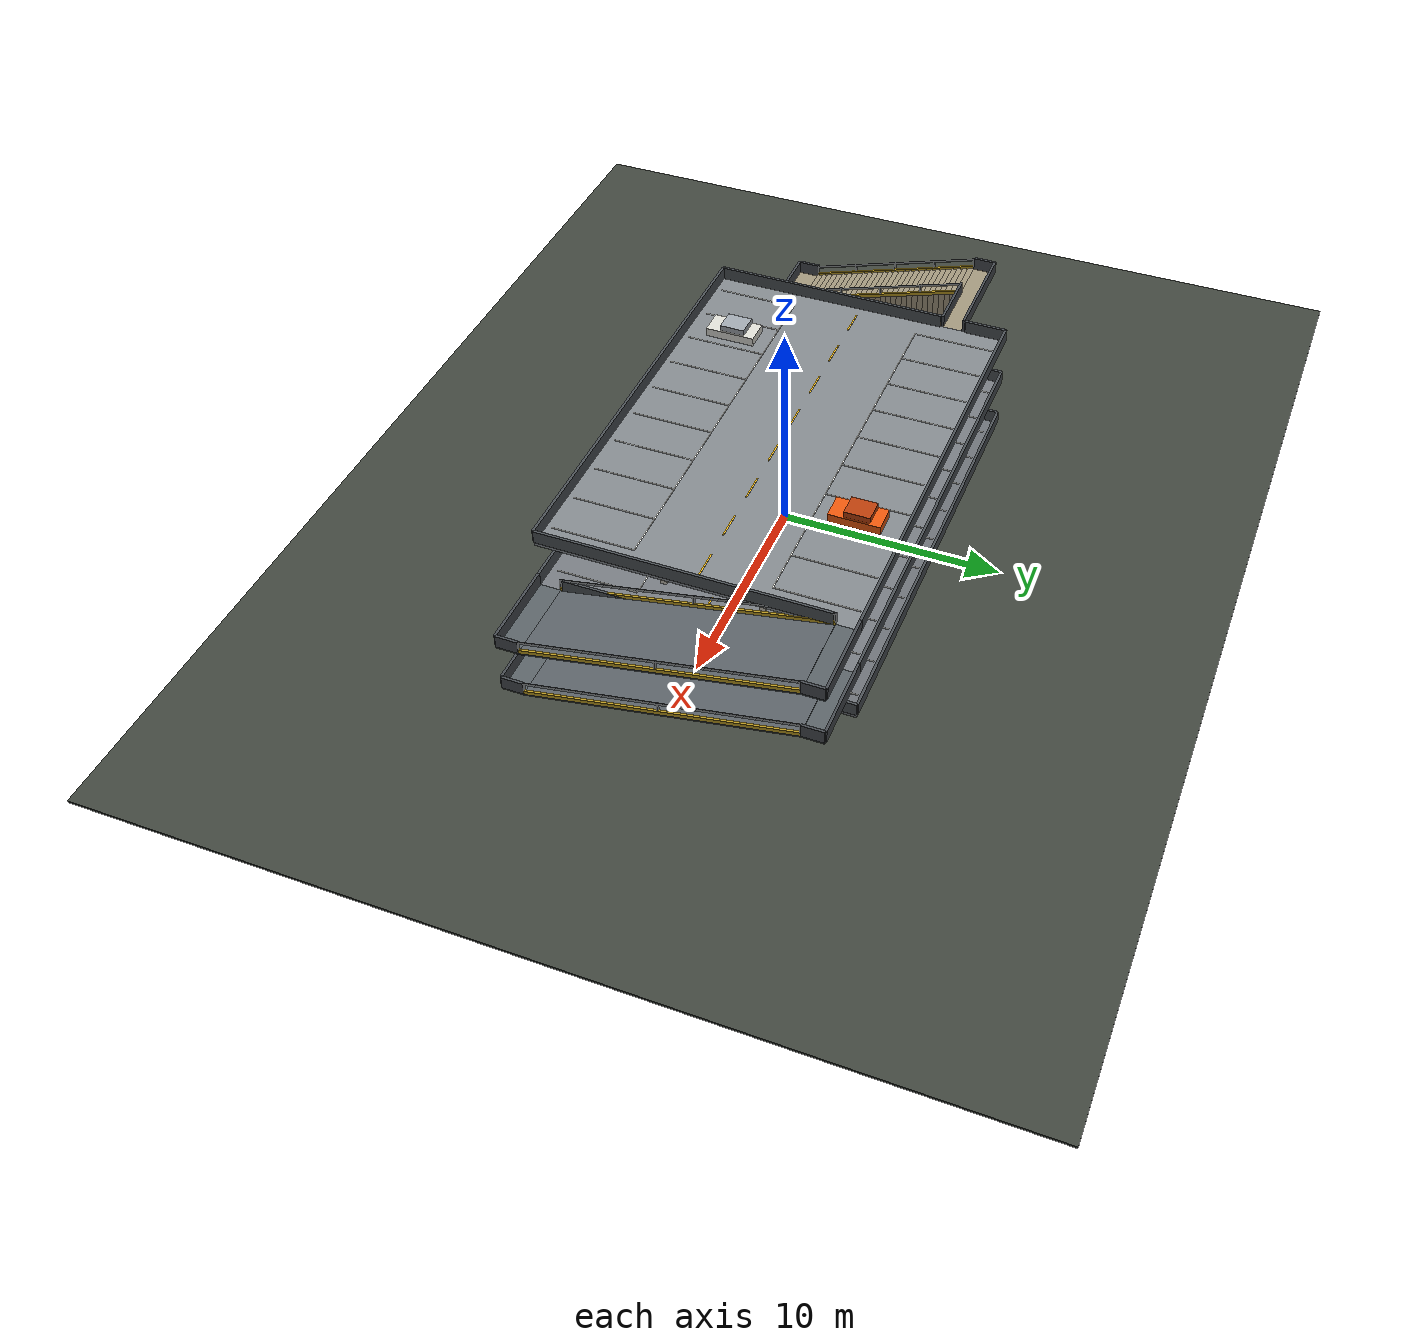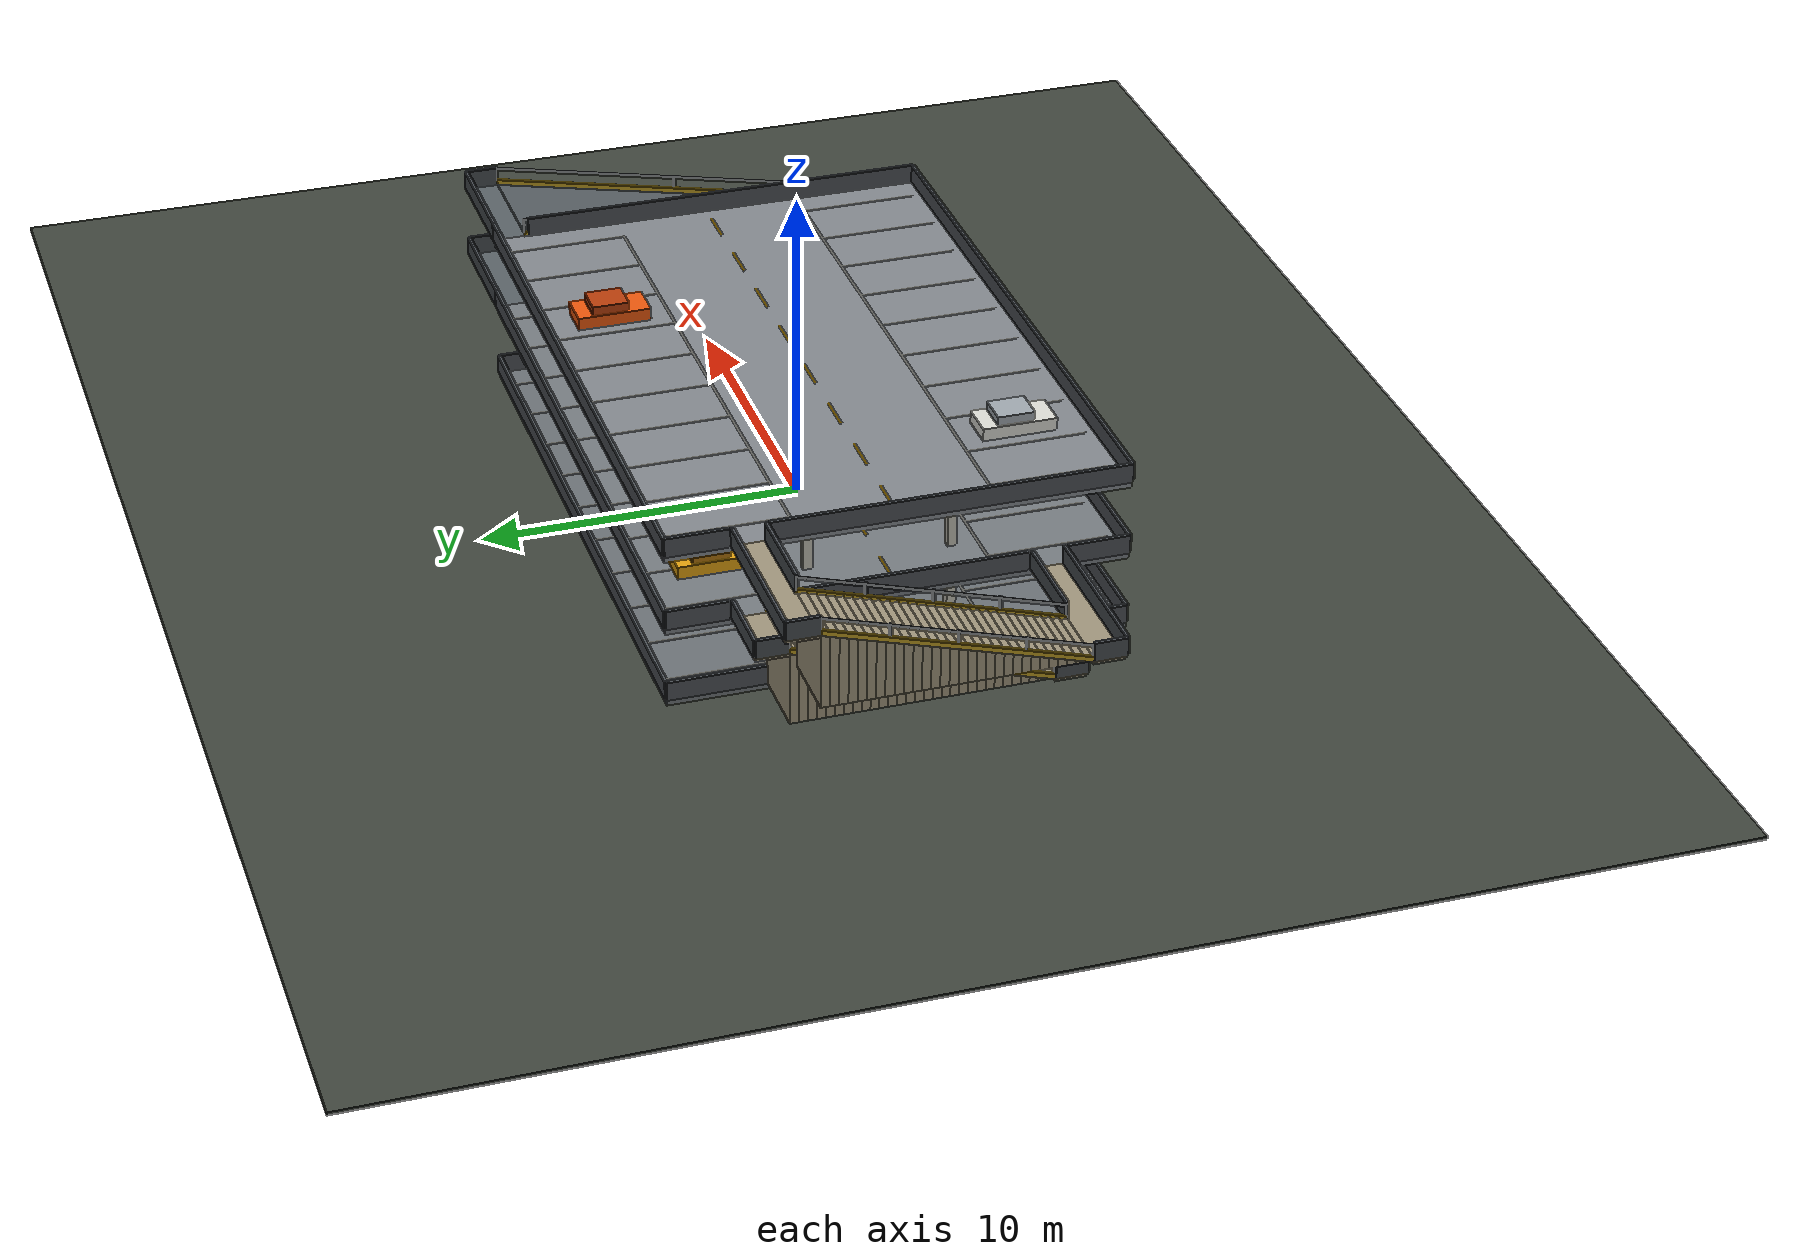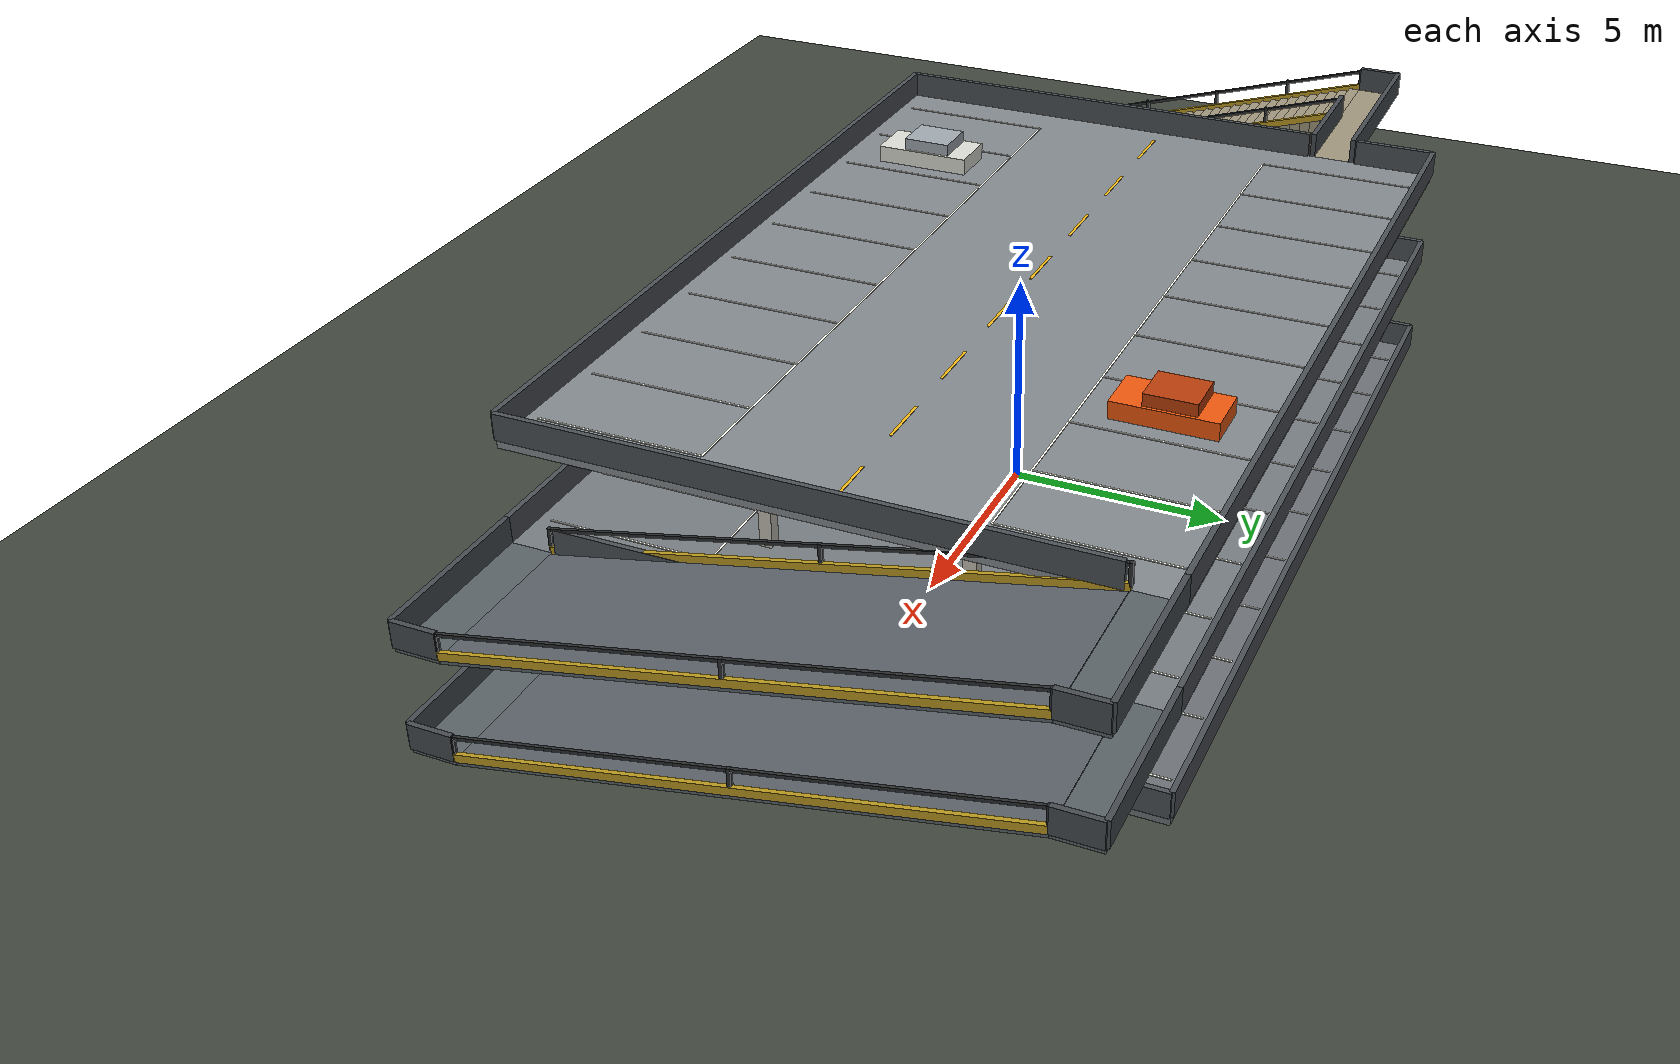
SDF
<?xml version='1.0'?>
<sdf version='1.7'>
  <world name='three_level_parking_garage'>
    <light name='sun' type='directional'>
      <cast_shadows>true</cast_shadows>
      <pose>0 0 20 0 0 0</pose>
      <diffuse>0.85 0.85 0.82 1</diffuse>
      <specular>0.18 0.18 0.18 1</specular>
      <attenuation>
        <range>1000</range>
        <constant>0.9</constant>
        <linear>0.01</linear>
        <quadratic>0.001</quadratic>
      </attenuation>
      <direction>-0.45 0.25 -0.86</direction>
    </light>

    <!-- Ceiling lights keep both covered decks readable with shadows enabled. -->
    <light name='level_1_light_west' type='point'>
      <pose>-5 0 2.06 0 0 0</pose><cast_shadows>false</cast_shadows>
      <diffuse>0.95 0.94 0.84 1</diffuse><specular>0.1 0.1 0.1 1</specular>
      <attenuation><range>12</range><constant>0.7</constant><linear>0.08</linear><quadratic>0.02</quadratic></attenuation>
    </light>
    <light name='level_1_light_east' type='point'>
      <pose>5 0 2.06 0 0 0</pose><cast_shadows>false</cast_shadows>
      <diffuse>0.95 0.94 0.84 1</diffuse><specular>0.1 0.1 0.1 1</specular>
      <attenuation><range>12</range><constant>0.7</constant><linear>0.08</linear><quadratic>0.02</quadratic></attenuation>
    </light>
    <light name='level_2_light_west' type='point'>
      <pose>-5 0 4.46 0 0 0</pose><cast_shadows>false</cast_shadows>
      <diffuse>0.92 0.95 1 1</diffuse><specular>0.1 0.1 0.1 1</specular>
      <attenuation><range>12</range><constant>0.7</constant><linear>0.08</linear><quadratic>0.02</quadratic></attenuation>
    </light>
    <light name='level_2_light_east' type='point'>
      <pose>5 0 4.46 0 0 0</pose><cast_shadows>false</cast_shadows>
      <diffuse>0.92 0.95 1 1</diffuse><specular>0.1 0.1 0.1 1</specular>
      <attenuation><range>12</range><constant>0.7</constant><linear>0.08</linear><quadratic>0.02</quadratic></attenuation>
    </light>

    <gravity>0 0 -9.8</gravity>
    <magnetic_field>6e-06 2.3e-05 -4.2e-05</magnetic_field>
    <atmosphere type='adiabatic'/>
    <physics type='ode'>
      <max_step_size>0.002</max_step_size>
      <real_time_factor>1</real_time_factor>
      <real_time_update_rate>500</real_time_update_rate>
      <ode>
        <solver><type>quick</type><iters>25</iters><sor>1.0</sor></solver>
        <constraints>
          <cfm>0</cfm><erp>0.2</erp>
          <contact_max_correcting_vel>100</contact_max_correcting_vel>
          <contact_surface_layer>0.001</contact_surface_layer>
        </constraints>
      </ode>
    </physics>
    <plugin name='gazebo_ros_state' filename='libgazebo_ros_state.so'>
      <ros><namespace>/</namespace></ros>
      <update_rate>10.0</update_rate>
    </plugin>
    <scene>
      <ambient>0.42 0.44 0.47 1</ambient>
      <background>0.72 0.77 0.82 1</background>
      <shadows>true</shadows>
      <grid>false</grid>
    </scene>

    <!-- Ground is deliberately below the deck so it cannot create duplicate contacts. -->
    <model name='site_ground'>
      <static>true</static>
      <link name='ground'>
        <pose>0 0 -0.27 0 0 0</pose>
        <collision name='collision'><geometry><box><size>50 40 0.10</size></box></geometry></collision>
        <visual name='visual'>
          <geometry><box><size>50 40 0.10</size></box></geometry>
          <material><ambient>0.20 0.22 0.20 1</ambient><diffuse>0.25 0.27 0.24 1</diffuse></material>
        </visual>
      </link>
    </model>

    <model name='three_level_parking_structure'>
      <static>true</static>

      <!-- Three vertically aligned 20 m x 14 m parking decks. -->
      <link name='parking_decks'>
        <collision name='floor_1_collision'>
          <pose>0 0 -0.10 0 0 0</pose><geometry><box><size>20 14 0.20</size></box></geometry>
          <surface><friction><ode><mu>20</mu><mu2>20</mu2></ode></friction></surface>
        </collision>
        <visual name='floor_1_visual'>
          <pose>0 0 -0.10 0 0 0</pose><geometry><box><size>20 14 0.20</size></box></geometry>
          <material><ambient>0.36 0.38 0.40 1</ambient><diffuse>0.42 0.44 0.46 1</diffuse></material>
        </visual>
        <collision name='floor_2_collision'>
          <pose>0 0 2.30 0 0 0</pose><geometry><box><size>20 14 0.20</size></box></geometry>
          <surface><friction><ode><mu>20</mu><mu2>20</mu2></ode></friction></surface>
        </collision>
        <visual name='floor_2_visual'>
          <pose>0 0 2.30 0 0 0</pose><geometry><box><size>20 14 0.20</size></box></geometry>
          <material><ambient>0.40 0.42 0.44 1</ambient><diffuse>0.46 0.48 0.50 1</diffuse></material>
        </visual>
        <collision name='floor_3_collision'>
          <pose>0 0 4.70 0 0 0</pose><geometry><box><size>20 14 0.20</size></box></geometry>
          <surface><friction><ode><mu>20</mu><mu2>20</mu2></ode></friction></surface>
        </collision>
        <visual name='floor_3_visual'>
          <pose>0 0 4.70 0 0 0</pose><geometry><box><size>20 14 0.20</size></box></geometry>
          <material><ambient>0.45 0.47 0.49 1</ambient><diffuse>0.51 0.53 0.55 1</diffuse></material>
        </visual>
      </link>

      <!-- East vehicle route: one ramp and two turn landings for each level change. -->
      <link name='ramps_and_landings'>
        <collision name='ramp_12_collision'>
          <pose>11.9 0 1.1412 0 -0.197396 1.570796</pose>
          <geometry><box><size>12.237648 3.8 0.12</size></box></geometry>
          <surface><friction><ode><mu>30</mu><mu2>30</mu2></ode></friction></surface>
        </collision>
        <visual name='ramp_12_visual'>
          <pose>11.9 0 1.1412 0 -0.197396 1.570796</pose>
          <geometry><box><size>12.237648 3.8 0.12</size></box></geometry>
          <material><ambient>0.30 0.33 0.35 1</ambient><diffuse>0.35 0.38 0.40 1</diffuse></material>
        </visual>
        <collision name='ramp_23_collision'>
          <pose>11.9 0 3.5412 0 -0.197396 1.570796</pose>
          <geometry><box><size>12.237648 3.8 0.12</size></box></geometry>
          <surface><friction><ode><mu>30</mu><mu2>30</mu2></ode></friction></surface>
        </collision>
        <visual name='ramp_23_visual'>
          <pose>11.9 0 3.5412 0 -0.197396 1.570796</pose>
          <geometry><box><size>12.237648 3.8 0.12</size></box></geometry>
          <material><ambient>0.30 0.33 0.35 1</ambient><diffuse>0.35 0.38 0.40 1</diffuse></material>
        </visual>

        <collision name='ramp_12_lower_landing_collision'><pose>11.9 -6.5 -0.06 0 0 0</pose><geometry><box><size>3.8 1.0 0.12</size></box></geometry></collision>
        <visual name='ramp_12_lower_landing_visual'><pose>11.9 -6.5 -0.06 0 0 0</pose><geometry><box><size>3.8 1.0 0.12</size></box></geometry><material><ambient>0.30 0.33 0.35 1</ambient><diffuse>0.35 0.38 0.40 1</diffuse></material></visual>
        <collision name='ramp_12_upper_landing_collision'><pose>11.9 6.5 2.34 0 0 0</pose><geometry><box><size>3.8 1.0 0.12</size></box></geometry></collision>
        <visual name='ramp_12_upper_landing_visual'><pose>11.9 6.5 2.34 0 0 0</pose><geometry><box><size>3.8 1.0 0.12</size></box></geometry><material><ambient>0.30 0.33 0.35 1</ambient><diffuse>0.35 0.38 0.40 1</diffuse></material></visual>
        <collision name='ramp_23_lower_landing_collision'><pose>11.9 -6.5 2.34 0 0 0</pose><geometry><box><size>3.8 1.0 0.12</size></box></geometry></collision>
        <visual name='ramp_23_lower_landing_visual'><pose>11.9 -6.5 2.34 0 0 0</pose><geometry><box><size>3.8 1.0 0.12</size></box></geometry><material><ambient>0.30 0.33 0.35 1</ambient><diffuse>0.35 0.38 0.40 1</diffuse></material></visual>
        <collision name='ramp_23_upper_landing_collision'><pose>11.9 6.5 4.74 0 0 0</pose><geometry><box><size>3.8 1.0 0.12</size></box></geometry></collision>
        <visual name='ramp_23_upper_landing_visual'><pose>11.9 6.5 4.74 0 0 0</pose><geometry><box><size>3.8 1.0 0.12</size></box></geometry><material><ambient>0.30 0.33 0.35 1</ambient><diffuse>0.35 0.38 0.40 1</diffuse></material></visual>
      </link>

      <!-- West pedestrian/robot route landings; the 30-step flights are below. -->
      <link name='stair_landings'>
        <collision name='stair_12_lower_landing_collision'><pose>-11.1 -4.5 -0.06 0 0 0</pose><geometry><box><size>2.2 1.0 0.12</size></box></geometry></collision>
        <visual name='stair_12_lower_landing_visual'><pose>-11.1 -4.5 -0.06 0 0 0</pose><geometry><box><size>2.2 1.0 0.12</size></box></geometry><material><ambient>0.54 0.51 0.43 1</ambient><diffuse>0.62 0.58 0.48 1</diffuse></material></visual>
        <collision name='stair_12_upper_landing_collision'><pose>-11.1 4.5 2.34 0 0 0</pose><geometry><box><size>2.2 1.0 0.12</size></box></geometry></collision>
        <visual name='stair_12_upper_landing_visual'><pose>-11.1 4.5 2.34 0 0 0</pose><geometry><box><size>2.2 1.0 0.12</size></box></geometry><material><ambient>0.54 0.51 0.43 1</ambient><diffuse>0.62 0.58 0.48 1</diffuse></material></visual>
        <!-- The upper flight is offset farther west so it cannot reduce headroom above the lower flight. -->
        <collision name='stair_23_lower_landing_collision'><pose>-12.55 -4.5 2.34 0 0 0</pose><geometry><box><size>5.1 1.0 0.12</size></box></geometry></collision>
        <visual name='stair_23_lower_landing_visual'><pose>-12.55 -4.5 2.34 0 0 0</pose><geometry><box><size>5.1 1.0 0.12</size></box></geometry><material><ambient>0.54 0.51 0.43 1</ambient><diffuse>0.62 0.58 0.48 1</diffuse></material></visual>
        <collision name='stair_23_upper_landing_collision'><pose>-12.55 4.5 4.74 0 0 0</pose><geometry><box><size>5.1 1.0 0.12</size></box></geometry></collision>
        <visual name='stair_23_upper_landing_visual'><pose>-12.55 4.5 4.74 0 0 0</pose><geometry><box><size>5.1 1.0 0.12</size></box></geometry><material><ambient>0.54 0.51 0.43 1</ambient><diffuse>0.62 0.58 0.48 1</diffuse></material></visual>
      </link>

      <!-- Stair geometry: 30 shallow steps per floor change. -->
      <link name='stairs'>
        <!-- Level 1 to level 2: 30 steps, 0.267 m tread x 0.08 m rise. -->
        <collision name='stair_12_step_01_collision'><pose>-11.1 -3.866667 0.040 0 0 0</pose><geometry><box><size>2.2 0.266668 0.080</size></box></geometry><surface><friction><ode><mu>30</mu><mu2>30</mu2></ode></friction></surface></collision>
        <visual name='stair_12_step_01_visual'><pose>-11.1 -3.866667 0.040 0 0 0</pose><geometry><box><size>2.2 0.266668 0.080</size></box></geometry><material><ambient>0.54 0.51 0.43 1</ambient><diffuse>0.62 0.58 0.48 1</diffuse></material></visual>
        <collision name='stair_12_step_02_collision'><pose>-11.1 -3.600000 0.080 0 0 0</pose><geometry><box><size>2.2 0.266668 0.160</size></box></geometry><surface><friction><ode><mu>30</mu><mu2>30</mu2></ode></friction></surface></collision>
        <visual name='stair_12_step_02_visual'><pose>-11.1 -3.600000 0.080 0 0 0</pose><geometry><box><size>2.2 0.266668 0.160</size></box></geometry><material><ambient>0.54 0.51 0.43 1</ambient><diffuse>0.62 0.58 0.48 1</diffuse></material></visual>
        <collision name='stair_12_step_03_collision'><pose>-11.1 -3.333333 0.120 0 0 0</pose><geometry><box><size>2.2 0.266668 0.240</size></box></geometry><surface><friction><ode><mu>30</mu><mu2>30</mu2></ode></friction></surface></collision>
        <visual name='stair_12_step_03_visual'><pose>-11.1 -3.333333 0.120 0 0 0</pose><geometry><box><size>2.2 0.266668 0.240</size></box></geometry><material><ambient>0.54 0.51 0.43 1</ambient><diffuse>0.62 0.58 0.48 1</diffuse></material></visual>
        <collision name='stair_12_step_04_collision'><pose>-11.1 -3.066667 0.160 0 0 0</pose><geometry><box><size>2.2 0.266668 0.320</size></box></geometry><surface><friction><ode><mu>30</mu><mu2>30</mu2></ode></friction></surface></collision>
        <visual name='stair_12_step_04_visual'><pose>-11.1 -3.066667 0.160 0 0 0</pose><geometry><box><size>2.2 0.266668 0.320</size></box></geometry><material><ambient>0.54 0.51 0.43 1</ambient><diffuse>0.62 0.58 0.48 1</diffuse></material></visual>
        <collision name='stair_12_step_05_collision'><pose>-11.1 -2.800000 0.200 0 0 0</pose><geometry><box><size>2.2 0.266668 0.400</size></box></geometry><surface><friction><ode><mu>30</mu><mu2>30</mu2></ode></friction></surface></collision>
        <visual name='stair_12_step_05_visual'><pose>-11.1 -2.800000 0.200 0 0 0</pose><geometry><box><size>2.2 0.266668 0.400</size></box></geometry><material><ambient>0.54 0.51 0.43 1</ambient><diffuse>0.62 0.58 0.48 1</diffuse></material></visual>
        <collision name='stair_12_step_06_collision'><pose>-11.1 -2.533333 0.240 0 0 0</pose><geometry><box><size>2.2 0.266668 0.480</size></box></geometry><surface><friction><ode><mu>30</mu><mu2>30</mu2></ode></friction></surface></collision>
        <visual name='stair_12_step_06_visual'><pose>-11.1 -2.533333 0.240 0 0 0</pose><geometry><box><size>2.2 0.266668 0.480</size></box></geometry><material><ambient>0.54 0.51 0.43 1</ambient><diffuse>0.62 0.58 0.48 1</diffuse></material></visual>
        <collision name='stair_12_step_07_collision'><pose>-11.1 -2.266667 0.280 0 0 0</pose><geometry><box><size>2.2 0.266668 0.560</size></box></geometry><surface><friction><ode><mu>30</mu><mu2>30</mu2></ode></friction></surface></collision>
        <visual name='stair_12_step_07_visual'><pose>-11.1 -2.266667 0.280 0 0 0</pose><geometry><box><size>2.2 0.266668 0.560</size></box></geometry><material><ambient>0.54 0.51 0.43 1</ambient><diffuse>0.62 0.58 0.48 1</diffuse></material></visual>
        <collision name='stair_12_step_08_collision'><pose>-11.1 -2.000000 0.320 0 0 0</pose><geometry><box><size>2.2 0.266668 0.640</size></box></geometry><surface><friction><ode><mu>30</mu><mu2>30</mu2></ode></friction></surface></collision>
        <visual name='stair_12_step_08_visual'><pose>-11.1 -2.000000 0.320 0 0 0</pose><geometry><box><size>2.2 0.266668 0.640</size></box></geometry><material><ambient>0.54 0.51 0.43 1</ambient><diffuse>0.62 0.58 0.48 1</diffuse></material></visual>
        <collision name='stair_12_step_09_collision'><pose>-11.1 -1.733333 0.360 0 0 0</pose><geometry><box><size>2.2 0.266668 0.720</size></box></geometry><surface><friction><ode><mu>30</mu><mu2>30</mu2></ode></friction></surface></collision>
        <visual name='stair_12_step_09_visual'><pose>-11.1 -1.733333 0.360 0 0 0</pose><geometry><box><size>2.2 0.266668 0.720</size></box></geometry><material><ambient>0.54 0.51 0.43 1</ambient><diffuse>0.62 0.58 0.48 1</diffuse></material></visual>
        <collision name='stair_12_step_10_collision'><pose>-11.1 -1.466667 0.400 0 0 0</pose><geometry><box><size>2.2 0.266668 0.800</size></box></geometry><surface><friction><ode><mu>30</mu><mu2>30</mu2></ode></friction></surface></collision>
        <visual name='stair_12_step_10_visual'><pose>-11.1 -1.466667 0.400 0 0 0</pose><geometry><box><size>2.2 0.266668 0.800</size></box></geometry><material><ambient>0.54 0.51 0.43 1</ambient><diffuse>0.62 0.58 0.48 1</diffuse></material></visual>
        <collision name='stair_12_step_11_collision'><pose>-11.1 -1.200000 0.440 0 0 0</pose><geometry><box><size>2.2 0.266668 0.880</size></box></geometry><surface><friction><ode><mu>30</mu><mu2>30</mu2></ode></friction></surface></collision>
        <visual name='stair_12_step_11_visual'><pose>-11.1 -1.200000 0.440 0 0 0</pose><geometry><box><size>2.2 0.266668 0.880</size></box></geometry><material><ambient>0.54 0.51 0.43 1</ambient><diffuse>0.62 0.58 0.48 1</diffuse></material></visual>
        <collision name='stair_12_step_12_collision'><pose>-11.1 -0.933333 0.480 0 0 0</pose><geometry><box><size>2.2 0.266668 0.960</size></box></geometry><surface><friction><ode><mu>30</mu><mu2>30</mu2></ode></friction></surface></collision>
        <visual name='stair_12_step_12_visual'><pose>-11.1 -0.933333 0.480 0 0 0</pose><geometry><box><size>2.2 0.266668 0.960</size></box></geometry><material><ambient>0.54 0.51 0.43 1</ambient><diffuse>0.62 0.58 0.48 1</diffuse></material></visual>
        <collision name='stair_12_step_13_collision'><pose>-11.1 -0.666667 0.520 0 0 0</pose><geometry><box><size>2.2 0.266668 1.040</size></box></geometry><surface><friction><ode><mu>30</mu><mu2>30</mu2></ode></friction></surface></collision>
        <visual name='stair_12_step_13_visual'><pose>-11.1 -0.666667 0.520 0 0 0</pose><geometry><box><size>2.2 0.266668 1.040</size></box></geometry><material><ambient>0.54 0.51 0.43 1</ambient><diffuse>0.62 0.58 0.48 1</diffuse></material></visual>
        <collision name='stair_12_step_14_collision'><pose>-11.1 -0.400000 0.560 0 0 0</pose><geometry><box><size>2.2 0.266668 1.120</size></box></geometry><surface><friction><ode><mu>30</mu><mu2>30</mu2></ode></friction></surface></collision>
        <visual name='stair_12_step_14_visual'><pose>-11.1 -0.400000 0.560 0 0 0</pose><geometry><box><size>2.2 0.266668 1.120</size></box></geometry><material><ambient>0.54 0.51 0.43 1</ambient><diffuse>0.62 0.58 0.48 1</diffuse></material></visual>
        <collision name='stair_12_step_15_collision'><pose>-11.1 -0.133333 0.600 0 0 0</pose><geometry><box><size>2.2 0.266668 1.200</size></box></geometry><surface><friction><ode><mu>30</mu><mu2>30</mu2></ode></friction></surface></collision>
        <visual name='stair_12_step_15_visual'><pose>-11.1 -0.133333 0.600 0 0 0</pose><geometry><box><size>2.2 0.266668 1.200</size></box></geometry><material><ambient>0.54 0.51 0.43 1</ambient><diffuse>0.62 0.58 0.48 1</diffuse></material></visual>
        <collision name='stair_12_step_16_collision'><pose>-11.1 0.133333 0.640 0 0 0</pose><geometry><box><size>2.2 0.266668 1.280</size></box></geometry><surface><friction><ode><mu>30</mu><mu2>30</mu2></ode></friction></surface></collision>
        <visual name='stair_12_step_16_visual'><pose>-11.1 0.133333 0.640 0 0 0</pose><geometry><box><size>2.2 0.266668 1.280</size></box></geometry><material><ambient>0.54 0.51 0.43 1</ambient><diffuse>0.62 0.58 0.48 1</diffuse></material></visual>
        <collision name='stair_12_step_17_collision'><pose>-11.1 0.400000 0.680 0 0 0</pose><geometry><box><size>2.2 0.266668 1.360</size></box></geometry><surface><friction><ode><mu>30</mu><mu2>30</mu2></ode></friction></surface></collision>
        <visual name='stair_12_step_17_visual'><pose>-11.1 0.400000 0.680 0 0 0</pose><geometry><box><size>2.2 0.266668 1.360</size></box></geometry><material><ambient>0.54 0.51 0.43 1</ambient><diffuse>0.62 0.58 0.48 1</diffuse></material></visual>
        <collision name='stair_12_step_18_collision'><pose>-11.1 0.666667 0.720 0 0 0</pose><geometry><box><size>2.2 0.266668 1.440</size></box></geometry><surface><friction><ode><mu>30</mu><mu2>30</mu2></ode></friction></surface></collision>
        <visual name='stair_12_step_18_visual'><pose>-11.1 0.666667 0.720 0 0 0</pose><geometry><box><size>2.2 0.266668 1.440</size></box></geometry><material><ambient>0.54 0.51 0.43 1</ambient><diffuse>0.62 0.58 0.48 1</diffuse></material></visual>
        <collision name='stair_12_step_19_collision'><pose>-11.1 0.933333 0.760 0 0 0</pose><geometry><box><size>2.2 0.266668 1.520</size></box></geometry><surface><friction><ode><mu>30</mu><mu2>30</mu2></ode></friction></surface></collision>
        <visual name='stair_12_step_19_visual'><pose>-11.1 0.933333 0.760 0 0 0</pose><geometry><box><size>2.2 0.266668 1.520</size></box></geometry><material><ambient>0.54 0.51 0.43 1</ambient><diffuse>0.62 0.58 0.48 1</diffuse></material></visual>
        <collision name='stair_12_step_20_collision'><pose>-11.1 1.200000 0.800 0 0 0</pose><geometry><box><size>2.2 0.266668 1.600</size></box></geometry><surface><friction><ode><mu>30</mu><mu2>30</mu2></ode></friction></surface></collision>
        <visual name='stair_12_step_20_visual'><pose>-11.1 1.200000 0.800 0 0 0</pose><geometry><box><size>2.2 0.266668 1.600</size></box></geometry><material><ambient>0.54 0.51 0.43 1</ambient><diffuse>0.62 0.58 0.48 1</diffuse></material></visual>
        <collision name='stair_12_step_21_collision'><pose>-11.1 1.466667 0.840 0 0 0</pose><geometry><box><size>2.2 0.266668 1.680</size></box></geometry><surface><friction><ode><mu>30</mu><mu2>30</mu2></ode></friction></surface></collision>
        <visual name='stair_12_step_21_visual'><pose>-11.1 1.466667 0.840 0 0 0</pose><geometry><box><size>2.2 0.266668 1.680</size></box></geometry><material><ambient>0.54 0.51 0.43 1</ambient><diffuse>0.62 0.58 0.48 1</diffuse></material></visual>
        <collision name='stair_12_step_22_collision'><pose>-11.1 1.733333 0.880 0 0 0</pose><geometry><box><size>2.2 0.266668 1.760</size></box></geometry><surface><friction><ode><mu>30</mu><mu2>30</mu2></ode></friction></surface></collision>
        <visual name='stair_12_step_22_visual'><pose>-11.1 1.733333 0.880 0 0 0</pose><geometry><box><size>2.2 0.266668 1.760</size></box></geometry><material><ambient>0.54 0.51 0.43 1</ambient><diffuse>0.62 0.58 0.48 1</diffuse></material></visual>
        <collision name='stair_12_step_23_collision'><pose>-11.1 2.000000 0.920 0 0 0</pose><geometry><box><size>2.2 0.266668 1.840</size></box></geometry><surface><friction><ode><mu>30</mu><mu2>30</mu2></ode></friction></surface></collision>
        <visual name='stair_12_step_23_visual'><pose>-11.1 2.000000 0.920 0 0 0</pose><geometry><box><size>2.2 0.266668 1.840</size></box></geometry><material><ambient>0.54 0.51 0.43 1</ambient><diffuse>0.62 0.58 0.48 1</diffuse></material></visual>
        <collision name='stair_12_step_24_collision'><pose>-11.1 2.266667 0.960 0 0 0</pose><geometry><box><size>2.2 0.266668 1.920</size></box></geometry><surface><friction><ode><mu>30</mu><mu2>30</mu2></ode></friction></surface></collision>
        <visual name='stair_12_step_24_visual'><pose>-11.1 2.266667 0.960 0 0 0</pose><geometry><box><size>2.2 0.266668 1.920</size></box></geometry><material><ambient>0.54 0.51 0.43 1</ambient><diffuse>0.62 0.58 0.48 1</diffuse></material></visual>
        <collision name='stair_12_step_25_collision'><pose>-11.1 2.533333 1.000 0 0 0</pose><geometry><box><size>2.2 0.266668 2.000</size></box></geometry><surface><friction><ode><mu>30</mu><mu2>30</mu2></ode></friction></surface></collision>
        <visual name='stair_12_step_25_visual'><pose>-11.1 2.533333 1.000 0 0 0</pose><geometry><box><size>2.2 0.266668 2.000</size></box></geometry><material><ambient>0.54 0.51 0.43 1</ambient><diffuse>0.62 0.58 0.48 1</diffuse></material></visual>
        <collision name='stair_12_step_26_collision'><pose>-11.1 2.800000 1.040 0 0 0</pose><geometry><box><size>2.2 0.266668 2.080</size></box></geometry><surface><friction><ode><mu>30</mu><mu2>30</mu2></ode></friction></surface></collision>
        <visual name='stair_12_step_26_visual'><pose>-11.1 2.800000 1.040 0 0 0</pose><geometry><box><size>2.2 0.266668 2.080</size></box></geometry><material><ambient>0.54 0.51 0.43 1</ambient><diffuse>0.62 0.58 0.48 1</diffuse></material></visual>
        <collision name='stair_12_step_27_collision'><pose>-11.1 3.066667 1.080 0 0 0</pose><geometry><box><size>2.2 0.266668 2.160</size></box></geometry><surface><friction><ode><mu>30</mu><mu2>30</mu2></ode></friction></surface></collision>
        <visual name='stair_12_step_27_visual'><pose>-11.1 3.066667 1.080 0 0 0</pose><geometry><box><size>2.2 0.266668 2.160</size></box></geometry><material><ambient>0.54 0.51 0.43 1</ambient><diffuse>0.62 0.58 0.48 1</diffuse></material></visual>
        <collision name='stair_12_step_28_collision'><pose>-11.1 3.333333 1.120 0 0 0</pose><geometry><box><size>2.2 0.266668 2.240</size></box></geometry><surface><friction><ode><mu>30</mu><mu2>30</mu2></ode></friction></surface></collision>
        <visual name='stair_12_step_28_visual'><pose>-11.1 3.333333 1.120 0 0 0</pose><geometry><box><size>2.2 0.266668 2.240</size></box></geometry><material><ambient>0.54 0.51 0.43 1</ambient><diffuse>0.62 0.58 0.48 1</diffuse></material></visual>
        <collision name='stair_12_step_29_collision'><pose>-11.1 3.600000 1.160 0 0 0</pose><geometry><box><size>2.2 0.266668 2.320</size></box></geometry><surface><friction><ode><mu>30</mu><mu2>30</mu2></ode></friction></surface></collision>
        <visual name='stair_12_step_29_visual'><pose>-11.1 3.600000 1.160 0 0 0</pose><geometry><box><size>2.2 0.266668 2.320</size></box></geometry><material><ambient>0.54 0.51 0.43 1</ambient><diffuse>0.62 0.58 0.48 1</diffuse></material></visual>
        <collision name='stair_12_step_30_collision'><pose>-11.1 3.866667 1.200 0 0 0</pose><geometry><box><size>2.2 0.266668 2.400</size></box></geometry><surface><friction><ode><mu>30</mu><mu2>30</mu2></ode></friction></surface></collision>
        <visual name='stair_12_step_30_visual'><pose>-11.1 3.866667 1.200 0 0 0</pose><geometry><box><size>2.2 0.266668 2.400</size></box></geometry><material><ambient>0.54 0.51 0.43 1</ambient><diffuse>0.62 0.58 0.48 1</diffuse></material></visual>
        <!-- Level 2 to level 3: 30 steps, 0.267 m tread x 0.08 m rise. -->
        <collision name='stair_23_step_01_collision'><pose>-14.0 -3.866667 2.440 0 0 0</pose><geometry><box><size>2.2 0.266668 0.080</size></box></geometry><surface><friction><ode><mu>30</mu><mu2>30</mu2></ode></friction></surface></collision>
        <visual name='stair_23_step_01_visual'><pose>-14.0 -3.866667 2.440 0 0 0</pose><geometry><box><size>2.2 0.266668 0.080</size></box></geometry><material><ambient>0.54 0.51 0.43 1</ambient><diffuse>0.62 0.58 0.48 1</diffuse></material></visual>
        <collision name='stair_23_step_02_collision'><pose>-14.0 -3.600000 2.480 0 0 0</pose><geometry><box><size>2.2 0.266668 0.160</size></box></geometry><surface><friction><ode><mu>30</mu><mu2>30</mu2></ode></friction></surface></collision>
        <visual name='stair_23_step_02_visual'><pose>-14.0 -3.600000 2.480 0 0 0</pose><geometry><box><size>2.2 0.266668 0.160</size></box></geometry><material><ambient>0.54 0.51 0.43 1</ambient><diffuse>0.62 0.58 0.48 1</diffuse></material></visual>
        <collision name='stair_23_step_03_collision'><pose>-14.0 -3.333333 2.520 0 0 0</pose><geometry><box><size>2.2 0.266668 0.240</size></box></geometry><surface><friction><ode><mu>30</mu><mu2>30</mu2></ode></friction></surface></collision>
        <visual name='stair_23_step_03_visual'><pose>-14.0 -3.333333 2.520 0 0 0</pose><geometry><box><size>2.2 0.266668 0.240</size></box></geometry><material><ambient>0.54 0.51 0.43 1</ambient><diffuse>0.62 0.58 0.48 1</diffuse></material></visual>
        <collision name='stair_23_step_04_collision'><pose>-14.0 -3.066667 2.560 0 0 0</pose><geometry><box><size>2.2 0.266668 0.320</size></box></geometry><surface><friction><ode><mu>30</mu><mu2>30</mu2></ode></friction></surface></collision>
        <visual name='stair_23_step_04_visual'><pose>-14.0 -3.066667 2.560 0 0 0</pose><geometry><box><size>2.2 0.266668 0.320</size></box></geometry><material><ambient>0.54 0.51 0.43 1</ambient><diffuse>0.62 0.58 0.48 1</diffuse></material></visual>
        <collision name='stair_23_step_05_collision'><pose>-14.0 -2.800000 2.600 0 0 0</pose><geometry><box><size>2.2 0.266668 0.400</size></box></geometry><surface><friction><ode><mu>30</mu><mu2>30</mu2></ode></friction></surface></collision>
        <visual name='stair_23_step_05_visual'><pose>-14.0 -2.800000 2.600 0 0 0</pose><geometry><box><size>2.2 0.266668 0.400</size></box></geometry><material><ambient>0.54 0.51 0.43 1</ambient><diffuse>0.62 0.58 0.48 1</diffuse></material></visual>
        <collision name='stair_23_step_06_collision'><pose>-14.0 -2.533333 2.640 0 0 0</pose><geometry><box><size>2.2 0.266668 0.480</size></box></geometry><surface><friction><ode><mu>30</mu><mu2>30</mu2></ode></friction></surface></collision>
        <visual name='stair_23_step_06_visual'><pose>-14.0 -2.533333 2.640 0 0 0</pose><geometry><box><size>2.2 0.266668 0.480</size></box></geometry><material><ambient>0.54 0.51 0.43 1</ambient><diffuse>0.62 0.58 0.48 1</diffuse></material></visual>
        <collision name='stair_23_step_07_collision'><pose>-14.0 -2.266667 2.680 0 0 0</pose><geometry><box><size>2.2 0.266668 0.560</size></box></geometry><surface><friction><ode><mu>30</mu><mu2>30</mu2></ode></friction></surface></collision>
        <visual name='stair_23_step_07_visual'><pose>-14.0 -2.266667 2.680 0 0 0</pose><geometry><box><size>2.2 0.266668 0.560</size></box></geometry><material><ambient>0.54 0.51 0.43 1</ambient><diffuse>0.62 0.58 0.48 1</diffuse></material></visual>
        <collision name='stair_23_step_08_collision'><pose>-14.0 -2.000000 2.720 0 0 0</pose><geometry><box><size>2.2 0.266668 0.640</size></box></geometry><surface><friction><ode><mu>30</mu><mu2>30</mu2></ode></friction></surface></collision>
        <visual name='stair_23_step_08_visual'><pose>-14.0 -2.000000 2.720 0 0 0</pose><geometry><box><size>2.2 0.266668 0.640</size></box></geometry><material><ambient>0.54 0.51 0.43 1</ambient><diffuse>0.62 0.58 0.48 1</diffuse></material></visual>
        <collision name='stair_23_step_09_collision'><pose>-14.0 -1.733333 2.760 0 0 0</pose><geometry><box><size>2.2 0.266668 0.720</size></box></geometry><surface><friction><ode><mu>30</mu><mu2>30</mu2></ode></friction></surface></collision>
        <visual name='stair_23_step_09_visual'><pose>-14.0 -1.733333 2.760 0 0 0</pose><geometry><box><size>2.2 0.266668 0.720</size></box></geometry><material><ambient>0.54 0.51 0.43 1</ambient><diffuse>0.62 0.58 0.48 1</diffuse></material></visual>
        <collision name='stair_23_step_10_collision'><pose>-14.0 -1.466667 2.800 0 0 0</pose><geometry><box><size>2.2 0.266668 0.800</size></box></geometry><surface><friction><ode><mu>30</mu><mu2>30</mu2></ode></friction></surface></collision>
        <visual name='stair_23_step_10_visual'><pose>-14.0 -1.466667 2.800 0 0 0</pose><geometry><box><size>2.2 0.266668 0.800</size></box></geometry><material><ambient>0.54 0.51 0.43 1</ambient><diffuse>0.62 0.58 0.48 1</diffuse></material></visual>
        <collision name='stair_23_step_11_collision'><pose>-14.0 -1.200000 2.840 0 0 0</pose><geometry><box><size>2.2 0.266668 0.880</size></box></geometry><surface><friction><ode><mu>30</mu><mu2>30</mu2></ode></friction></surface></collision>
        <visual name='stair_23_step_11_visual'><pose>-14.0 -1.200000 2.840 0 0 0</pose><geometry><box><size>2.2 0.266668 0.880</size></box></geometry><material><ambient>0.54 0.51 0.43 1</ambient><diffuse>0.62 0.58 0.48 1</diffuse></material></visual>
        <collision name='stair_23_step_12_collision'><pose>-14.0 -0.933333 2.880 0 0 0</pose><geometry><box><size>2.2 0.266668 0.960</size></box></geometry><surface><friction><ode><mu>30</mu><mu2>30</mu2></ode></friction></surface></collision>
        <visual name='stair_23_step_12_visual'><pose>-14.0 -0.933333 2.880 0 0 0</pose><geometry><box><size>2.2 0.266668 0.960</size></box></geometry><material><ambient>0.54 0.51 0.43 1</ambient><diffuse>0.62 0.58 0.48 1</diffuse></material></visual>
        <collision name='stair_23_step_13_collision'><pose>-14.0 -0.666667 2.920 0 0 0</pose><geometry><box><size>2.2 0.266668 1.040</size></box></geometry><surface><friction><ode><mu>30</mu><mu2>30</mu2></ode></friction></surface></collision>
        <visual name='stair_23_step_13_visual'><pose>-14.0 -0.666667 2.920 0 0 0</pose><geometry><box><size>2.2 0.266668 1.040</size></box></geometry><material><ambient>0.54 0.51 0.43 1</ambient><diffuse>0.62 0.58 0.48 1</diffuse></material></visual>
        <collision name='stair_23_step_14_collision'><pose>-14.0 -0.400000 2.960 0 0 0</pose><geometry><box><size>2.2 0.266668 1.120</size></box></geometry><surface><friction><ode><mu>30</mu><mu2>30</mu2></ode></friction></surface></collision>
        <visual name='stair_23_step_14_visual'><pose>-14.0 -0.400000 2.960 0 0 0</pose><geometry><box><size>2.2 0.266668 1.120</size></box></geometry><material><ambient>0.54 0.51 0.43 1</ambient><diffuse>0.62 0.58 0.48 1</diffuse></material></visual>
        <collision name='stair_23_step_15_collision'><pose>-14.0 -0.133333 3.000 0 0 0</pose><geometry><box><size>2.2 0.266668 1.200</size></box></geometry><surface><friction><ode><mu>30</mu><mu2>30</mu2></ode></friction></surface></collision>
        <visual name='stair_23_step_15_visual'><pose>-14.0 -0.133333 3.000 0 0 0</pose><geometry><box><size>2.2 0.266668 1.200</size></box></geometry><material><ambient>0.54 0.51 0.43 1</ambient><diffuse>0.62 0.58 0.48 1</diffuse></material></visual>
        <collision name='stair_23_step_16_collision'><pose>-14.0 0.133333 3.040 0 0 0</pose><geometry><box><size>2.2 0.266668 1.280</size></box></geometry><surface><friction><ode><mu>30</mu><mu2>30</mu2></ode></friction></surface></collision>
        <visual name='stair_23_step_16_visual'><pose>-14.0 0.133333 3.040 0 0 0</pose><geometry><box><size>2.2 0.266668 1.280</size></box></geometry><material><ambient>0.54 0.51 0.43 1</ambient><diffuse>0.62 0.58 0.48 1</diffuse></material></visual>
        <collision name='stair_23_step_17_collision'><pose>-14.0 0.400000 3.080 0 0 0</pose><geometry><box><size>2.2 0.266668 1.360</size></box></geometry><surface><friction><ode><mu>30</mu><mu2>30</mu2></ode></friction></surface></collision>
        <visual name='stair_23_step_17_visual'><pose>-14.0 0.400000 3.080 0 0 0</pose><geometry><box><size>2.2 0.266668 1.360</size></box></geometry><material><ambient>0.54 0.51 0.43 1</ambient><diffuse>0.62 0.58 0.48 1</diffuse></material></visual>
        <collision name='stair_23_step_18_collision'><pose>-14.0 0.666667 3.120 0 0 0</pose><geometry><box><size>2.2 0.266668 1.440</size></box></geometry><surface><friction><ode><mu>30</mu><mu2>30</mu2></ode></friction></surface></collision>
        <visual name='stair_23_step_18_visual'><pose>-14.0 0.666667 3.120 0 0 0</pose><geometry><box><size>2.2 0.266668 1.440</size></box></geometry><material><ambient>0.54 0.51 0.43 1</ambient><diffuse>0.62 0.58 0.48 1</diffuse></material></visual>
        <collision name='stair_23_step_19_collision'><pose>-14.0 0.933333 3.160 0 0 0</pose><geometry><box><size>2.2 0.266668 1.520</size></box></geometry><surface><friction><ode><mu>30</mu><mu2>30</mu2></ode></friction></surface></collision>
        <visual name='stair_23_step_19_visual'><pose>-14.0 0.933333 3.160 0 0 0</pose><geometry><box><size>2.2 0.266668 1.520</size></box></geometry><material><ambient>0.54 0.51 0.43 1</ambient><diffuse>0.62 0.58 0.48 1</diffuse></material></visual>
        <collision name='stair_23_step_20_collision'><pose>-14.0 1.200000 3.200 0 0 0</pose><geometry><box><size>2.2 0.266668 1.600</size></box></geometry><surface><friction><ode><mu>30</mu><mu2>30</mu2></ode></friction></surface></collision>
        <visual name='stair_23_step_20_visual'><pose>-14.0 1.200000 3.200 0 0 0</pose><geometry><box><size>2.2 0.266668 1.600</size></box></geometry><material><ambient>0.54 0.51 0.43 1</ambient><diffuse>0.62 0.58 0.48 1</diffuse></material></visual>
        <collision name='stair_23_step_21_collision'><pose>-14.0 1.466667 3.240 0 0 0</pose><geometry><box><size>2.2 0.266668 1.680</size></box></geometry><surface><friction><ode><mu>30</mu><mu2>30</mu2></ode></friction></surface></collision>
        <visual name='stair_23_step_21_visual'><pose>-14.0 1.466667 3.240 0 0 0</pose><geometry><box><size>2.2 0.266668 1.680</size></box></geometry><material><ambient>0.54 0.51 0.43 1</ambient><diffuse>0.62 0.58 0.48 1</diffuse></material></visual>
        <collision name='stair_23_step_22_collision'><pose>-14.0 1.733333 3.280 0 0 0</pose><geometry><box><size>2.2 0.266668 1.760</size></box></geometry><surface><friction><ode><mu>30</mu><mu2>30</mu2></ode></friction></surface></collision>
        <visual name='stair_23_step_22_visual'><pose>-14.0 1.733333 3.280 0 0 0</pose><geometry><box><size>2.2 0.266668 1.760</size></box></geometry><material><ambient>0.54 0.51 0.43 1</ambient><diffuse>0.62 0.58 0.48 1</diffuse></material></visual>
        <collision name='stair_23_step_23_collision'><pose>-14.0 2.000000 3.320 0 0 0</pose><geometry><box><size>2.2 0.266668 1.840</size></box></geometry><surface><friction><ode><mu>30</mu><mu2>30</mu2></ode></friction></surface></collision>
        <visual name='stair_23_step_23_visual'><pose>-14.0 2.000000 3.320 0 0 0</pose><geometry><box><size>2.2 0.266668 1.840</size></box></geometry><material><ambient>0.54 0.51 0.43 1</ambient><diffuse>0.62 0.58 0.48 1</diffuse></material></visual>
        <collision name='stair_23_step_24_collision'><pose>-14.0 2.266667 3.360 0 0 0</pose><geometry><box><size>2.2 0.266668 1.920</size></box></geometry><surface><friction><ode><mu>30</mu><mu2>30</mu2></ode></friction></surface></collision>
        <visual name='stair_23_step_24_visual'><pose>-14.0 2.266667 3.360 0 0 0</pose><geometry><box><size>2.2 0.266668 1.920</size></box></geometry><material><ambient>0.54 0.51 0.43 1</ambient><diffuse>0.62 0.58 0.48 1</diffuse></material></visual>
        <collision name='stair_23_step_25_collision'><pose>-14.0 2.533333 3.400 0 0 0</pose><geometry><box><size>2.2 0.266668 2.000</size></box></geometry><surface><friction><ode><mu>30</mu><mu2>30</mu2></ode></friction></surface></collision>
        <visual name='stair_23_step_25_visual'><pose>-14.0 2.533333 3.400 0 0 0</pose><geometry><box><size>2.2 0.266668 2.000</size></box></geometry><material><ambient>0.54 0.51 0.43 1</ambient><diffuse>0.62 0.58 0.48 1</diffuse></material></visual>
        <collision name='stair_23_step_26_collision'><pose>-14.0 2.800000 3.440 0 0 0</pose><geometry><box><size>2.2 0.266668 2.080</size></box></geometry><surface><friction><ode><mu>30</mu><mu2>30</mu2></ode></friction></surface></collision>
        <visual name='stair_23_step_26_visual'><pose>-14.0 2.800000 3.440 0 0 0</pose><geometry><box><size>2.2 0.266668 2.080</size></box></geometry><material><ambient>0.54 0.51 0.43 1</ambient><diffuse>0.62 0.58 0.48 1</diffuse></material></visual>
        <collision name='stair_23_step_27_collision'><pose>-14.0 3.066667 3.480 0 0 0</pose><geometry><box><size>2.2 0.266668 2.160</size></box></geometry><surface><friction><ode><mu>30</mu><mu2>30</mu2></ode></friction></surface></collision>
        <visual name='stair_23_step_27_visual'><pose>-14.0 3.066667 3.480 0 0 0</pose><geometry><box><size>2.2 0.266668 2.160</size></box></geometry><material><ambient>0.54 0.51 0.43 1</ambient><diffuse>0.62 0.58 0.48 1</diffuse></material></visual>
        <collision name='stair_23_step_28_collision'><pose>-14.0 3.333333 3.520 0 0 0</pose><geometry><box><size>2.2 0.266668 2.240</size></box></geometry><surface><friction><ode><mu>30</mu><mu2>30</mu2></ode></friction></surface></collision>
        <visual name='stair_23_step_28_visual'><pose>-14.0 3.333333 3.520 0 0 0</pose><geometry><box><size>2.2 0.266668 2.240</size></box></geometry><material><ambient>0.54 0.51 0.43 1</ambient><diffuse>0.62 0.58 0.48 1</diffuse></material></visual>
        <collision name='stair_23_step_29_collision'><pose>-14.0 3.600000 3.560 0 0 0</pose><geometry><box><size>2.2 0.266668 2.320</size></box></geometry><surface><friction><ode><mu>30</mu><mu2>30</mu2></ode></friction></surface></collision>
        <visual name='stair_23_step_29_visual'><pose>-14.0 3.600000 3.560 0 0 0</pose><geometry><box><size>2.2 0.266668 2.320</size></box></geometry><material><ambient>0.54 0.51 0.43 1</ambient><diffuse>0.62 0.58 0.48 1</diffuse></material></visual>
        <collision name='stair_23_step_30_collision'><pose>-14.0 3.866667 3.600 0 0 0</pose><geometry><box><size>2.2 0.266668 2.400</size></box></geometry><surface><friction><ode><mu>30</mu><mu2>30</mu2></ode></friction></surface></collision>
        <visual name='stair_23_step_30_visual'><pose>-14.0 3.866667 3.600 0 0 0</pose><geometry><box><size>2.2 0.266668 2.400</size></box></geometry><material><ambient>0.54 0.51 0.43 1</ambient><diffuse>0.62 0.58 0.48 1</diffuse></material></visual>
      </link>

      <!-- Concrete columns make the stacked decks read as an open parking garage. -->
      <link name='support_columns'>
        <collision name='column_01_collision'><pose>-8 -2.2 2.30 0 0 0</pose><geometry><box><size>0.28 0.28 4.60</size></box></geometry></collision>
        <visual name='column_01_visual'><pose>-8 -2.2 2.30 0 0 0</pose><geometry><box><size>0.28 0.28 4.60</size></box></geometry><material><ambient>0.68 0.67 0.62 1</ambient><diffuse>0.76 0.75 0.70 1</diffuse></material></visual>
        <collision name='column_02_collision'><pose>-4 -2.2 2.30 0 0 0</pose><geometry><box><size>0.28 0.28 4.60</size></box></geometry></collision>
        <visual name='column_02_visual'><pose>-4 -2.2 2.30 0 0 0</pose><geometry><box><size>0.28 0.28 4.60</size></box></geometry><material><ambient>0.68 0.67 0.62 1</ambient><diffuse>0.76 0.75 0.70 1</diffuse></material></visual>
        <collision name='column_03_collision'><pose>0 -2.2 2.30 0 0 0</pose><geometry><box><size>0.28 0.28 4.60</size></box></geometry></collision>
        <visual name='column_03_visual'><pose>0 -2.2 2.30 0 0 0</pose><geometry><box><size>0.28 0.28 4.60</size></box></geometry><material><ambient>0.68 0.67 0.62 1</ambient><diffuse>0.76 0.75 0.70 1</diffuse></material></visual>
        <collision name='column_04_collision'><pose>4 -2.2 2.30 0 0 0</pose><geometry><box><size>0.28 0.28 4.60</size></box></geometry></collision>
        <visual name='column_04_visual'><pose>4 -2.2 2.30 0 0 0</pose><geometry><box><size>0.28 0.28 4.60</size></box></geometry><material><ambient>0.68 0.67 0.62 1</ambient><diffuse>0.76 0.75 0.70 1</diffuse></material></visual>
        <collision name='column_05_collision'><pose>8 -2.2 2.30 0 0 0</pose><geometry><box><size>0.28 0.28 4.60</size></box></geometry></collision>
        <visual name='column_05_visual'><pose>8 -2.2 2.30 0 0 0</pose><geometry><box><size>0.28 0.28 4.60</size></box></geometry><material><ambient>0.68 0.67 0.62 1</ambient><diffuse>0.76 0.75 0.70 1</diffuse></material></visual>
        <collision name='column_06_collision'><pose>-8 2.2 2.30 0 0 0</pose><geometry><box><size>0.28 0.28 4.60</size></box></geometry></collision>
        <visual name='column_06_visual'><pose>-8 2.2 2.30 0 0 0</pose><geometry><box><size>0.28 0.28 4.60</size></box></geometry><material><ambient>0.68 0.67 0.62 1</ambient><diffuse>0.76 0.75 0.70 1</diffuse></material></visual>
        <collision name='column_07_collision'><pose>-4 2.2 2.30 0 0 0</pose><geometry><box><size>0.28 0.28 4.60</size></box></geometry></collision>
        <visual name='column_07_visual'><pose>-4 2.2 2.30 0 0 0</pose><geometry><box><size>0.28 0.28 4.60</size></box></geometry><material><ambient>0.68 0.67 0.62 1</ambient><diffuse>0.76 0.75 0.70 1</diffuse></material></visual>
        <collision name='column_08_collision'><pose>0 2.2 2.30 0 0 0</pose><geometry><box><size>0.28 0.28 4.60</size></box></geometry></collision>
        <visual name='column_08_visual'><pose>0 2.2 2.30 0 0 0</pose><geometry><box><size>0.28 0.28 4.60</size></box></geometry><material><ambient>0.68 0.67 0.62 1</ambient><diffuse>0.76 0.75 0.70 1</diffuse></material></visual>
        <collision name='column_09_collision'><pose>4 2.2 2.30 0 0 0</pose><geometry><box><size>0.28 0.28 4.60</size></box></geometry></collision>
        <visual name='column_09_visual'><pose>4 2.2 2.30 0 0 0</pose><geometry><box><size>0.28 0.28 4.60</size></box></geometry><material><ambient>0.68 0.67 0.62 1</ambient><diffuse>0.76 0.75 0.70 1</diffuse></material></visual>
        <collision name='column_10_collision'><pose>8 2.2 2.30 0 0 0</pose><geometry><box><size>0.28 0.28 4.60</size></box></geometry></collision>
        <visual name='column_10_visual'><pose>8 2.2 2.30 0 0 0</pose><geometry><box><size>0.28 0.28 4.60</size></box></geometry><material><ambient>0.68 0.67 0.62 1</ambient><diffuse>0.76 0.75 0.70 1</diffuse></material></visual>
      </link>

      <!-- Collision-enabled deck parapets and all connector guards. -->
      <link name='safety_guards'>
        <!-- Level-specific openings line up with the ramp and stair landings. -->
        <collision name='l1_north_guard_collision'><pose>0 7.0 0.30 0 0 0</pose><geometry><box><size>20.0 0.12 0.60</size></box></geometry></collision>
        <visual name='l1_north_guard_visual'><pose>0 7.0 0.30 0 0 0</pose><geometry><box><size>20.0 0.12 0.60</size></box></geometry><material><ambient>0.22 0.24 0.26 1</ambient><diffuse>0.29 0.31 0.33 1</diffuse></material></visual>
        <collision name='l1_south_guard_collision'><pose>0 -7.0 0.30 0 0 0</pose><geometry><box><size>20.0 0.12 0.60</size></box></geometry></collision>
        <visual name='l1_south_guard_visual'><pose>0 -7.0 0.30 0 0 0</pose><geometry><box><size>20.0 0.12 0.60</size></box></geometry><material><ambient>0.22 0.24 0.26 1</ambient><diffuse>0.29 0.31 0.33 1</diffuse></material></visual>
        <collision name='l2_north_guard_collision'><pose>0 7.0 2.70 0 0 0</pose><geometry><box><size>20.0 0.12 0.60</size></box></geometry></collision>
        <visual name='l2_north_guard_visual'><pose>0 7.0 2.70 0 0 0</pose><geometry><box><size>20.0 0.12 0.60</size></box></geometry><material><ambient>0.22 0.24 0.26 1</ambient><diffuse>0.29 0.31 0.33 1</diffuse></material></visual>
        <collision name='l2_south_guard_collision'><pose>0 -7.0 2.70 0 0 0</pose><geometry><box><size>20.0 0.12 0.60</size></box></geometry></collision>
        <visual name='l2_south_guard_visual'><pose>0 -7.0 2.70 0 0 0</pose><geometry><box><size>20.0 0.12 0.60</size></box></geometry><material><ambient>0.22 0.24 0.26 1</ambient><diffuse>0.29 0.31 0.33 1</diffuse></material></visual>
        <collision name='l3_north_guard_collision'><pose>0 7.0 5.10 0 0 0</pose><geometry><box><size>20.0 0.12 0.60</size></box></geometry></collision>
        <visual name='l3_north_guard_visual'><pose>0 7.0 5.10 0 0 0</pose><geometry><box><size>20.0 0.12 0.60</size></box></geometry><material><ambient>0.22 0.24 0.26 1</ambient><diffuse>0.29 0.31 0.33 1</diffuse></material></visual>
        <collision name='l3_south_guard_collision'><pose>0 -7.0 5.10 0 0 0</pose><geometry><box><size>20.0 0.12 0.60</size></box></geometry></collision>
        <visual name='l3_south_guard_visual'><pose>0 -7.0 5.10 0 0 0</pose><geometry><box><size>20.0 0.12 0.60</size></box></geometry><material><ambient>0.22 0.24 0.26 1</ambient><diffuse>0.29 0.31 0.33 1</diffuse></material></visual>
        <collision name='l1_east_guard_2_collision'><pose>10.0 0.55 0.30 0 0 0</pose><geometry><box><size>0.12 12.9 0.60</size></box></geometry></collision>
        <visual name='l1_east_guard_2_visual'><pose>10.0 0.55 0.30 0 0 0</pose><geometry><box><size>0.12 12.9 0.60</size></box></geometry><material><ambient>0.22 0.24 0.26 1</ambient><diffuse>0.29 0.31 0.33 1</diffuse></material></visual>
        <collision name='l1_west_guard_1_collision'><pose>-10.0 -6.05 0.30 0 0 0</pose><geometry><box><size>0.12 1.9 0.60</size></box></geometry></collision>
        <visual name='l1_west_guard_1_visual'><pose>-10.0 -6.05 0.30 0 0 0</pose><geometry><box><size>0.12 1.9 0.60</size></box></geometry><material><ambient>0.22 0.24 0.26 1</ambient><diffuse>0.29 0.31 0.33 1</diffuse></material></visual>
        <collision name='l1_west_guard_2_collision'><pose>-10.0 1.55 0.30 0 0 0</pose><geometry><box><size>0.12 10.9 0.60</size></box></geometry></collision>
        <visual name='l1_west_guard_2_visual'><pose>-10.0 1.55 0.30 0 0 0</pose><geometry><box><size>0.12 10.9 0.60</size></box></geometry><material><ambient>0.22 0.24 0.26 1</ambient><diffuse>0.29 0.31 0.33 1</diffuse></material></visual>
        <collision name='l2_east_guard_2_collision'><pose>10.0 0 2.70 0 0 0</pose><geometry><box><size>0.12 11.8 0.60</size></box></geometry></collision>
        <visual name='l2_east_guard_2_visual'><pose>10.0 0 2.70 0 0 0</pose><geometry><box><size>0.12 11.8 0.60</size></box></geometry><material><ambient>0.22 0.24 0.26 1</ambient><diffuse>0.29 0.31 0.33 1</diffuse></material></visual>
        <collision name='l2_west_guard_1_collision'><pose>-10.0 -6.05 2.70 0 0 0</pose><geometry><box><size>0.12 1.9 0.60</size></box></geometry></collision>
        <visual name='l2_west_guard_1_visual'><pose>-10.0 -6.05 2.70 0 0 0</pose><geometry><box><size>0.12 1.9 0.60</size></box></geometry><material><ambient>0.22 0.24 0.26 1</ambient><diffuse>0.29 0.31 0.33 1</diffuse></material></visual>
        <collision name='l2_west_guard_2_collision'><pose>-10.0 0 2.70 0 0 0</pose><geometry><box><size>0.12 7.8 0.60</size></box></geometry></collision>
        <visual name='l2_west_guard_2_visual'><pose>-10.0 0 2.70 0 0 0</pose><geometry><box><size>0.12 7.8 0.60</size></box></geometry><material><ambient>0.22 0.24 0.26 1</ambient><diffuse>0.29 0.31 0.33 1</diffuse></material></visual>
        <collision name='l2_west_guard_3_collision'><pose>-10.0 6.05 2.70 0 0 0</pose><geometry><box><size>0.12 1.9 0.60</size></box></geometry></collision>
        <visual name='l2_west_guard_3_visual'><pose>-10.0 6.05 2.70 0 0 0</pose><geometry><box><size>0.12 1.9 0.60</size></box></geometry><material><ambient>0.22 0.24 0.26 1</ambient><diffuse>0.29 0.31 0.33 1</diffuse></material></visual>
        <collision name='l3_east_guard_1_collision'><pose>10.0 -0.55 5.10 0 0 0</pose><geometry><box><size>0.12 12.9 0.60</size></box></geometry></collision>
        <visual name='l3_east_guard_1_visual'><pose>10.0 -0.55 5.10 0 0 0</pose><geometry><box><size>0.12 12.9 0.60</size></box></geometry><material><ambient>0.22 0.24 0.26 1</ambient><diffuse>0.29 0.31 0.33 1</diffuse></material></visual>
        <collision name='l3_west_guard_1_collision'><pose>-10.0 -1.55 5.10 0 0 0</pose><geometry><box><size>0.12 10.9 0.60</size></box></geometry></collision>
        <visual name='l3_west_guard_1_visual'><pose>-10.0 -1.55 5.10 0 0 0</pose><geometry><box><size>0.12 10.9 0.60</size></box></geometry><material><ambient>0.22 0.24 0.26 1</ambient><diffuse>0.29 0.31 0.33 1</diffuse></material></visual>
        <collision name='l3_west_guard_2_collision'><pose>-10.0 6.05 5.10 0 0 0</pose><geometry><box><size>0.12 1.9 0.60</size></box></geometry></collision>
        <visual name='l3_west_guard_2_visual'><pose>-10.0 6.05 5.10 0 0 0</pose><geometry><box><size>0.12 1.9 0.60</size></box></geometry><material><ambient>0.22 0.24 0.26 1</ambient><diffuse>0.29 0.31 0.33 1</diffuse></material></visual>
        <!-- Ramp 1 to 2: low curb, top rail and vertical posts on both sides. -->
        <collision name='ramp_12_inner_curb_collision'><pose>10 0 1.28 0 -0.197396 1.570796</pose><geometry><box><size>12.237648 0.10 0.18</size></box></geometry></collision>
        <visual name='ramp_12_inner_curb_visual'><pose>10 0 1.28 0 -0.197396 1.570796</pose><geometry><box><size>12.237648 0.10 0.18</size></box></geometry><material><ambient>0.52 0.43 0.09 1</ambient><diffuse>0.72 0.59 0.12 1</diffuse></material></visual>
        <collision name='ramp_12_inner_rail_collision'><pose>10 0 1.75 0 -0.197396 1.570796</pose><geometry><box><size>12.237648 0.07 0.07</size></box></geometry></collision>
        <visual name='ramp_12_inner_rail_visual'><pose>10 0 1.75 0 -0.197396 1.570796</pose><geometry><box><size>12.237648 0.07 0.07</size></box></geometry><material><ambient>0.10 0.11 0.12 1</ambient><diffuse>0.16 0.17 0.18 1</diffuse></material></visual>
        <collision name='ramp_12_inner_post_1_collision'><pose>10 -6 0.34 0 0 0</pose><geometry><box><size>0.08 0.08 0.50</size></box></geometry></collision>
        <visual name='ramp_12_inner_post_1_visual'><pose>10 -6 0.34 0 0 0</pose><geometry><box><size>0.08 0.08 0.50</size></box></geometry><material><ambient>0.10 0.11 0.12 1</ambient><diffuse>0.16 0.17 0.18 1</diffuse></material></visual>
        <collision name='ramp_12_inner_post_2_collision'><pose>10 0 1.54 0 0 0</pose><geometry><box><size>0.08 0.08 0.50</size></box></geometry></collision>
        <visual name='ramp_12_inner_post_2_visual'><pose>10 0 1.54 0 0 0</pose><geometry><box><size>0.08 0.08 0.50</size></box></geometry><material><ambient>0.10 0.11 0.12 1</ambient><diffuse>0.16 0.17 0.18 1</diffuse></material></visual>
        <collision name='ramp_12_inner_post_3_collision'><pose>10 6 2.74 0 0 0</pose><geometry><box><size>0.08 0.08 0.50</size></box></geometry></collision>
        <visual name='ramp_12_inner_post_3_visual'><pose>10 6 2.74 0 0 0</pose><geometry><box><size>0.08 0.08 0.50</size></box></geometry><material><ambient>0.10 0.11 0.12 1</ambient><diffuse>0.16 0.17 0.18 1</diffuse></material></visual>
        <collision name='ramp_12_outer_curb_collision'><pose>13.8 0 1.28 0 -0.197396 1.570796</pose><geometry><box><size>12.237648 0.10 0.18</size></box></geometry></collision>
        <visual name='ramp_12_outer_curb_visual'><pose>13.8 0 1.28 0 -0.197396 1.570796</pose><geometry><box><size>12.237648 0.10 0.18</size></box></geometry><material><ambient>0.52 0.43 0.09 1</ambient><diffuse>0.72 0.59 0.12 1</diffuse></material></visual>
        <collision name='ramp_12_outer_rail_collision'><pose>13.8 0 1.75 0 -0.197396 1.570796</pose><geometry><box><size>12.237648 0.07 0.07</size></box></geometry></collision>
        <visual name='ramp_12_outer_rail_visual'><pose>13.8 0 1.75 0 -0.197396 1.570796</pose><geometry><box><size>12.237648 0.07 0.07</size></box></geometry><material><ambient>0.10 0.11 0.12 1</ambient><diffuse>0.16 0.17 0.18 1</diffuse></material></visual>
        <collision name='ramp_12_outer_post_1_collision'><pose>13.8 -6 0.34 0 0 0</pose><geometry><box><size>0.08 0.08 0.50</size></box></geometry></collision>
        <visual name='ramp_12_outer_post_1_visual'><pose>13.8 -6 0.34 0 0 0</pose><geometry><box><size>0.08 0.08 0.50</size></box></geometry><material><ambient>0.10 0.11 0.12 1</ambient><diffuse>0.16 0.17 0.18 1</diffuse></material></visual>
        <collision name='ramp_12_outer_post_2_collision'><pose>13.8 0 1.54 0 0 0</pose><geometry><box><size>0.08 0.08 0.50</size></box></geometry></collision>
        <visual name='ramp_12_outer_post_2_visual'><pose>13.8 0 1.54 0 0 0</pose><geometry><box><size>0.08 0.08 0.50</size></box></geometry><material><ambient>0.10 0.11 0.12 1</ambient><diffuse>0.16 0.17 0.18 1</diffuse></material></visual>
        <collision name='ramp_12_outer_post_3_collision'><pose>13.8 6 2.74 0 0 0</pose><geometry><box><size>0.08 0.08 0.50</size></box></geometry></collision>
        <visual name='ramp_12_outer_post_3_visual'><pose>13.8 6 2.74 0 0 0</pose><geometry><box><size>0.08 0.08 0.50</size></box></geometry><material><ambient>0.10 0.11 0.12 1</ambient><diffuse>0.16 0.17 0.18 1</diffuse></material></visual>
        <!-- Ramp 2 to 3: low curb, top rail and vertical posts on both sides. -->
        <collision name='ramp_23_inner_curb_collision'><pose>10 0 3.68 0 -0.197396 1.570796</pose><geometry><box><size>12.237648 0.10 0.18</size></box></geometry></collision>
        <visual name='ramp_23_inner_curb_visual'><pose>10 0 3.68 0 -0.197396 1.570796</pose><geometry><box><size>12.237648 0.10 0.18</size></box></geometry><material><ambient>0.52 0.43 0.09 1</ambient><diffuse>0.72 0.59 0.12 1</diffuse></material></visual>
        <collision name='ramp_23_inner_rail_collision'><pose>10 0 4.15 0 -0.197396 1.570796</pose><geometry><box><size>12.237648 0.07 0.07</size></box></geometry></collision>
        <visual name='ramp_23_inner_rail_visual'><pose>10 0 4.15 0 -0.197396 1.570796</pose><geometry><box><size>12.237648 0.07 0.07</size></box></geometry><material><ambient>0.10 0.11 0.12 1</ambient><diffuse>0.16 0.17 0.18 1</diffuse></material></visual>
        <collision name='ramp_23_inner_post_1_collision'><pose>10 -6 2.74 0 0 0</pose><geometry><box><size>0.08 0.08 0.50</size></box></geometry></collision>
        <visual name='ramp_23_inner_post_1_visual'><pose>10 -6 2.74 0 0 0</pose><geometry><box><size>0.08 0.08 0.50</size></box></geometry><material><ambient>0.10 0.11 0.12 1</ambient><diffuse>0.16 0.17 0.18 1</diffuse></material></visual>
        <collision name='ramp_23_inner_post_2_collision'><pose>10 0 3.94 0 0 0</pose><geometry><box><size>0.08 0.08 0.50</size></box></geometry></collision>
        <visual name='ramp_23_inner_post_2_visual'><pose>10 0 3.94 0 0 0</pose><geometry><box><size>0.08 0.08 0.50</size></box></geometry><material><ambient>0.10 0.11 0.12 1</ambient><diffuse>0.16 0.17 0.18 1</diffuse></material></visual>
        <collision name='ramp_23_inner_post_3_collision'><pose>10 6 5.14 0 0 0</pose><geometry><box><size>0.08 0.08 0.50</size></box></geometry></collision>
        <visual name='ramp_23_inner_post_3_visual'><pose>10 6 5.14 0 0 0</pose><geometry><box><size>0.08 0.08 0.50</size></box></geometry><material><ambient>0.10 0.11 0.12 1</ambient><diffuse>0.16 0.17 0.18 1</diffuse></material></visual>
        <collision name='ramp_23_outer_curb_collision'><pose>13.8 0 3.68 0 -0.197396 1.570796</pose><geometry><box><size>12.237648 0.10 0.18</size></box></geometry></collision>
        <visual name='ramp_23_outer_curb_visual'><pose>13.8 0 3.68 0 -0.197396 1.570796</pose><geometry><box><size>12.237648 0.10 0.18</size></box></geometry><material><ambient>0.52 0.43 0.09 1</ambient><diffuse>0.72 0.59 0.12 1</diffuse></material></visual>
        <collision name='ramp_23_outer_rail_collision'><pose>13.8 0 4.15 0 -0.197396 1.570796</pose><geometry><box><size>12.237648 0.07 0.07</size></box></geometry></collision>
        <visual name='ramp_23_outer_rail_visual'><pose>13.8 0 4.15 0 -0.197396 1.570796</pose><geometry><box><size>12.237648 0.07 0.07</size></box></geometry><material><ambient>0.10 0.11 0.12 1</ambient><diffuse>0.16 0.17 0.18 1</diffuse></material></visual>
        <collision name='ramp_23_outer_post_1_collision'><pose>13.8 -6 2.74 0 0 0</pose><geometry><box><size>0.08 0.08 0.50</size></box></geometry></collision>
        <visual name='ramp_23_outer_post_1_visual'><pose>13.8 -6 2.74 0 0 0</pose><geometry><box><size>0.08 0.08 0.50</size></box></geometry><material><ambient>0.10 0.11 0.12 1</ambient><diffuse>0.16 0.17 0.18 1</diffuse></material></visual>
        <collision name='ramp_23_outer_post_2_collision'><pose>13.8 0 3.94 0 0 0</pose><geometry><box><size>0.08 0.08 0.50</size></box></geometry></collision>
        <visual name='ramp_23_outer_post_2_visual'><pose>13.8 0 3.94 0 0 0</pose><geometry><box><size>0.08 0.08 0.50</size></box></geometry><material><ambient>0.10 0.11 0.12 1</ambient><diffuse>0.16 0.17 0.18 1</diffuse></material></visual>
        <collision name='ramp_23_outer_post_3_collision'><pose>13.8 6 5.14 0 0 0</pose><geometry><box><size>0.08 0.08 0.50</size></box></geometry></collision>
        <visual name='ramp_23_outer_post_3_visual'><pose>13.8 6 5.14 0 0 0</pose><geometry><box><size>0.08 0.08 0.50</size></box></geometry><material><ambient>0.10 0.11 0.12 1</ambient><diffuse>0.16 0.17 0.18 1</diffuse></material></visual>
        <!-- Stair 1 to 2: continuous guards following the step nosings. -->
        <collision name='stair_12_outer_curb_collision'><pose>-12.2 0 1.27 0 -0.291457 1.570796</pose><geometry><box><size>8.352245 0.10 0.16</size></box></geometry></collision>
        <visual name='stair_12_outer_curb_visual'><pose>-12.2 0 1.27 0 -0.291457 1.570796</pose><geometry><box><size>8.352245 0.10 0.16</size></box></geometry><material><ambient>0.52 0.43 0.09 1</ambient><diffuse>0.72 0.59 0.12 1</diffuse></material></visual>
        <collision name='stair_12_outer_rail_collision'><pose>-12.2 0 1.70 0 -0.291457 1.570796</pose><geometry><box><size>8.352245 0.07 0.07</size></box></geometry></collision>
        <visual name='stair_12_outer_rail_visual'><pose>-12.2 0 1.70 0 -0.291457 1.570796</pose><geometry><box><size>8.352245 0.07 0.07</size></box></geometry><material><ambient>0.10 0.11 0.12 1</ambient><diffuse>0.16 0.17 0.18 1</diffuse></material></visual>
        <collision name='stair_12_outer_post_1_collision'><pose>-12.2 -4 0.32 0 0 0</pose><geometry><box><size>0.08 0.08 0.48</size></box></geometry></collision>
        <visual name='stair_12_outer_post_1_visual'><pose>-12.2 -4 0.32 0 0 0</pose><geometry><box><size>0.08 0.08 0.48</size></box></geometry><material><ambient>0.10 0.11 0.12 1</ambient><diffuse>0.16 0.17 0.18 1</diffuse></material></visual>
        <collision name='stair_12_outer_post_2_collision'><pose>-12.2 -2 0.92 0 0 0</pose><geometry><box><size>0.08 0.08 0.48</size></box></geometry></collision>
        <visual name='stair_12_outer_post_2_visual'><pose>-12.2 -2 0.92 0 0 0</pose><geometry><box><size>0.08 0.08 0.48</size></box></geometry><material><ambient>0.10 0.11 0.12 1</ambient><diffuse>0.16 0.17 0.18 1</diffuse></material></visual>
        <collision name='stair_12_outer_post_3_collision'><pose>-12.2 0 1.52 0 0 0</pose><geometry><box><size>0.08 0.08 0.48</size></box></geometry></collision>
        <visual name='stair_12_outer_post_3_visual'><pose>-12.2 0 1.52 0 0 0</pose><geometry><box><size>0.08 0.08 0.48</size></box></geometry><material><ambient>0.10 0.11 0.12 1</ambient><diffuse>0.16 0.17 0.18 1</diffuse></material></visual>
        <collision name='stair_12_outer_post_4_collision'><pose>-12.2 2 2.12 0 0 0</pose><geometry><box><size>0.08 0.08 0.48</size></box></geometry></collision>
        <visual name='stair_12_outer_post_4_visual'><pose>-12.2 2 2.12 0 0 0</pose><geometry><box><size>0.08 0.08 0.48</size></box></geometry><material><ambient>0.10 0.11 0.12 1</ambient><diffuse>0.16 0.17 0.18 1</diffuse></material></visual>
        <collision name='stair_12_outer_post_5_collision'><pose>-12.2 4 2.72 0 0 0</pose><geometry><box><size>0.08 0.08 0.48</size></box></geometry></collision>
        <visual name='stair_12_outer_post_5_visual'><pose>-12.2 4 2.72 0 0 0</pose><geometry><box><size>0.08 0.08 0.48</size></box></geometry><material><ambient>0.10 0.11 0.12 1</ambient><diffuse>0.16 0.17 0.18 1</diffuse></material></visual>
        <collision name='stair_12_inner_curb_collision'><pose>-10 0 1.27 0 -0.291457 1.570796</pose><geometry><box><size>8.352245 0.10 0.16</size></box></geometry></collision>
        <visual name='stair_12_inner_curb_visual'><pose>-10 0 1.27 0 -0.291457 1.570796</pose><geometry><box><size>8.352245 0.10 0.16</size></box></geometry><material><ambient>0.52 0.43 0.09 1</ambient><diffuse>0.72 0.59 0.12 1</diffuse></material></visual>
        <collision name='stair_12_inner_rail_collision'><pose>-10 0 1.70 0 -0.291457 1.570796</pose><geometry><box><size>8.352245 0.07 0.07</size></box></geometry></collision>
        <visual name='stair_12_inner_rail_visual'><pose>-10 0 1.70 0 -0.291457 1.570796</pose><geometry><box><size>8.352245 0.07 0.07</size></box></geometry><material><ambient>0.10 0.11 0.12 1</ambient><diffuse>0.16 0.17 0.18 1</diffuse></material></visual>
        <collision name='stair_12_inner_post_1_collision'><pose>-10 -4 0.32 0 0 0</pose><geometry><box><size>0.08 0.08 0.48</size></box></geometry></collision>
        <visual name='stair_12_inner_post_1_visual'><pose>-10 -4 0.32 0 0 0</pose><geometry><box><size>0.08 0.08 0.48</size></box></geometry><material><ambient>0.10 0.11 0.12 1</ambient><diffuse>0.16 0.17 0.18 1</diffuse></material></visual>
        <collision name='stair_12_inner_post_2_collision'><pose>-10 -2 0.92 0 0 0</pose><geometry><box><size>0.08 0.08 0.48</size></box></geometry></collision>
        <visual name='stair_12_inner_post_2_visual'><pose>-10 -2 0.92 0 0 0</pose><geometry><box><size>0.08 0.08 0.48</size></box></geometry><material><ambient>0.10 0.11 0.12 1</ambient><diffuse>0.16 0.17 0.18 1</diffuse></material></visual>
        <collision name='stair_12_inner_post_3_collision'><pose>-10 0 1.52 0 0 0</pose><geometry><box><size>0.08 0.08 0.48</size></box></geometry></collision>
        <visual name='stair_12_inner_post_3_visual'><pose>-10 0 1.52 0 0 0</pose><geometry><box><size>0.08 0.08 0.48</size></box></geometry><material><ambient>0.10 0.11 0.12 1</ambient><diffuse>0.16 0.17 0.18 1</diffuse></material></visual>
        <collision name='stair_12_inner_post_4_collision'><pose>-10 2 2.12 0 0 0</pose><geometry><box><size>0.08 0.08 0.48</size></box></geometry></collision>
        <visual name='stair_12_inner_post_4_visual'><pose>-10 2 2.12 0 0 0</pose><geometry><box><size>0.08 0.08 0.48</size></box></geometry><material><ambient>0.10 0.11 0.12 1</ambient><diffuse>0.16 0.17 0.18 1</diffuse></material></visual>
        <collision name='stair_12_inner_post_5_collision'><pose>-10 4 2.72 0 0 0</pose><geometry><box><size>0.08 0.08 0.48</size></box></geometry></collision>
        <visual name='stair_12_inner_post_5_visual'><pose>-10 4 2.72 0 0 0</pose><geometry><box><size>0.08 0.08 0.48</size></box></geometry><material><ambient>0.10 0.11 0.12 1</ambient><diffuse>0.16 0.17 0.18 1</diffuse></material></visual>
        <!-- Stair 2 to 3: continuous guards following the step nosings. -->
        <collision name='stair_23_outer_curb_collision'><pose>-15.1 0 3.67 0 -0.291457 1.570796</pose><geometry><box><size>8.352245 0.10 0.16</size></box></geometry></collision>
        <visual name='stair_23_outer_curb_visual'><pose>-15.1 0 3.67 0 -0.291457 1.570796</pose><geometry><box><size>8.352245 0.10 0.16</size></box></geometry><material><ambient>0.52 0.43 0.09 1</ambient><diffuse>0.72 0.59 0.12 1</diffuse></material></visual>
        <collision name='stair_23_outer_rail_collision'><pose>-15.1 0 4.10 0 -0.291457 1.570796</pose><geometry><box><size>8.352245 0.07 0.07</size></box></geometry></collision>
        <visual name='stair_23_outer_rail_visual'><pose>-15.1 0 4.10 0 -0.291457 1.570796</pose><geometry><box><size>8.352245 0.07 0.07</size></box></geometry><material><ambient>0.10 0.11 0.12 1</ambient><diffuse>0.16 0.17 0.18 1</diffuse></material></visual>
        <collision name='stair_23_outer_post_1_collision'><pose>-15.1 -4 2.72 0 0 0</pose><geometry><box><size>0.08 0.08 0.48</size></box></geometry></collision>
        <visual name='stair_23_outer_post_1_visual'><pose>-15.1 -4 2.72 0 0 0</pose><geometry><box><size>0.08 0.08 0.48</size></box></geometry><material><ambient>0.10 0.11 0.12 1</ambient><diffuse>0.16 0.17 0.18 1</diffuse></material></visual>
        <collision name='stair_23_outer_post_2_collision'><pose>-15.1 -2 3.32 0 0 0</pose><geometry><box><size>0.08 0.08 0.48</size></box></geometry></collision>
        <visual name='stair_23_outer_post_2_visual'><pose>-15.1 -2 3.32 0 0 0</pose><geometry><box><size>0.08 0.08 0.48</size></box></geometry><material><ambient>0.10 0.11 0.12 1</ambient><diffuse>0.16 0.17 0.18 1</diffuse></material></visual>
        <collision name='stair_23_outer_post_3_collision'><pose>-15.1 0 3.92 0 0 0</pose><geometry><box><size>0.08 0.08 0.48</size></box></geometry></collision>
        <visual name='stair_23_outer_post_3_visual'><pose>-15.1 0 3.92 0 0 0</pose><geometry><box><size>0.08 0.08 0.48</size></box></geometry><material><ambient>0.10 0.11 0.12 1</ambient><diffuse>0.16 0.17 0.18 1</diffuse></material></visual>
        <collision name='stair_23_outer_post_4_collision'><pose>-15.1 2 4.52 0 0 0</pose><geometry><box><size>0.08 0.08 0.48</size></box></geometry></collision>
        <visual name='stair_23_outer_post_4_visual'><pose>-15.1 2 4.52 0 0 0</pose><geometry><box><size>0.08 0.08 0.48</size></box></geometry><material><ambient>0.10 0.11 0.12 1</ambient><diffuse>0.16 0.17 0.18 1</diffuse></material></visual>
        <collision name='stair_23_outer_post_5_collision'><pose>-15.1 4 5.12 0 0 0</pose><geometry><box><size>0.08 0.08 0.48</size></box></geometry></collision>
        <visual name='stair_23_outer_post_5_visual'><pose>-15.1 4 5.12 0 0 0</pose><geometry><box><size>0.08 0.08 0.48</size></box></geometry><material><ambient>0.10 0.11 0.12 1</ambient><diffuse>0.16 0.17 0.18 1</diffuse></material></visual>
        <collision name='stair_23_inner_curb_collision'><pose>-12.9 0 3.67 0 -0.291457 1.570796</pose><geometry><box><size>8.352245 0.10 0.16</size></box></geometry></collision>
        <visual name='stair_23_inner_curb_visual'><pose>-12.9 0 3.67 0 -0.291457 1.570796</pose><geometry><box><size>8.352245 0.10 0.16</size></box></geometry><material><ambient>0.52 0.43 0.09 1</ambient><diffuse>0.72 0.59 0.12 1</diffuse></material></visual>
        <collision name='stair_23_inner_rail_collision'><pose>-12.9 0 4.10 0 -0.291457 1.570796</pose><geometry><box><size>8.352245 0.07 0.07</size></box></geometry></collision>
        <visual name='stair_23_inner_rail_visual'><pose>-12.9 0 4.10 0 -0.291457 1.570796</pose><geometry><box><size>8.352245 0.07 0.07</size></box></geometry><material><ambient>0.10 0.11 0.12 1</ambient><diffuse>0.16 0.17 0.18 1</diffuse></material></visual>
        <collision name='stair_23_inner_post_1_collision'><pose>-12.9 -4 2.72 0 0 0</pose><geometry><box><size>0.08 0.08 0.48</size></box></geometry></collision>
        <visual name='stair_23_inner_post_1_visual'><pose>-12.9 -4 2.72 0 0 0</pose><geometry><box><size>0.08 0.08 0.48</size></box></geometry><material><ambient>0.10 0.11 0.12 1</ambient><diffuse>0.16 0.17 0.18 1</diffuse></material></visual>
        <collision name='stair_23_inner_post_2_collision'><pose>-12.9 -2 3.32 0 0 0</pose><geometry><box><size>0.08 0.08 0.48</size></box></geometry></collision>
        <visual name='stair_23_inner_post_2_visual'><pose>-12.9 -2 3.32 0 0 0</pose><geometry><box><size>0.08 0.08 0.48</size></box></geometry><material><ambient>0.10 0.11 0.12 1</ambient><diffuse>0.16 0.17 0.18 1</diffuse></material></visual>
        <collision name='stair_23_inner_post_3_collision'><pose>-12.9 0 3.92 0 0 0</pose><geometry><box><size>0.08 0.08 0.48</size></box></geometry></collision>
        <visual name='stair_23_inner_post_3_visual'><pose>-12.9 0 3.92 0 0 0</pose><geometry><box><size>0.08 0.08 0.48</size></box></geometry><material><ambient>0.10 0.11 0.12 1</ambient><diffuse>0.16 0.17 0.18 1</diffuse></material></visual>
        <collision name='stair_23_inner_post_4_collision'><pose>-12.9 2 4.52 0 0 0</pose><geometry><box><size>0.08 0.08 0.48</size></box></geometry></collision>
        <visual name='stair_23_inner_post_4_visual'><pose>-12.9 2 4.52 0 0 0</pose><geometry><box><size>0.08 0.08 0.48</size></box></geometry><material><ambient>0.10 0.11 0.12 1</ambient><diffuse>0.16 0.17 0.18 1</diffuse></material></visual>
        <collision name='stair_23_inner_post_5_collision'><pose>-12.9 4 5.12 0 0 0</pose><geometry><box><size>0.08 0.08 0.48</size></box></geometry></collision>
        <visual name='stair_23_inner_post_5_visual'><pose>-12.9 4 5.12 0 0 0</pose><geometry><box><size>0.08 0.08 0.48</size></box></geometry><material><ambient>0.10 0.11 0.12 1</ambient><diffuse>0.16 0.17 0.18 1</diffuse></material></visual>
        <collision name='ramp_12_lower_landing_south_guard_collision'><pose>11.9 -7.0 0.30 0 0 0</pose><geometry><box><size>3.8 0.12 0.60</size></box></geometry></collision>
        <visual name='ramp_12_lower_landing_south_guard_visual'><pose>11.9 -7.0 0.30 0 0 0</pose><geometry><box><size>3.8 0.12 0.60</size></box></geometry><material><ambient>0.19 0.21 0.23 1</ambient><diffuse>0.27 0.29 0.31 1</diffuse></material></visual>
        <collision name='ramp_12_lower_landing_outer_guard_collision'><pose>13.8 -6.5 0.30 0 0 0</pose><geometry><box><size>0.12 1.0 0.60</size></box></geometry></collision>
        <visual name='ramp_12_lower_landing_outer_guard_visual'><pose>13.8 -6.5 0.30 0 0 0</pose><geometry><box><size>0.12 1.0 0.60</size></box></geometry><material><ambient>0.19 0.21 0.23 1</ambient><diffuse>0.27 0.29 0.31 1</diffuse></material></visual>
        <collision name='ramp_12_upper_landing_north_guard_collision'><pose>11.9 7.0 2.70 0 0 0</pose><geometry><box><size>3.8 0.12 0.60</size></box></geometry></collision>
        <visual name='ramp_12_upper_landing_north_guard_visual'><pose>11.9 7.0 2.70 0 0 0</pose><geometry><box><size>3.8 0.12 0.60</size></box></geometry><material><ambient>0.19 0.21 0.23 1</ambient><diffuse>0.27 0.29 0.31 1</diffuse></material></visual>
        <collision name='ramp_12_upper_landing_outer_guard_collision'><pose>13.8 6.5 2.70 0 0 0</pose><geometry><box><size>0.12 1.0 0.60</size></box></geometry></collision>
        <visual name='ramp_12_upper_landing_outer_guard_visual'><pose>13.8 6.5 2.70 0 0 0</pose><geometry><box><size>0.12 1.0 0.60</size></box></geometry><material><ambient>0.19 0.21 0.23 1</ambient><diffuse>0.27 0.29 0.31 1</diffuse></material></visual>
        <collision name='stair_12_lower_landing_south_guard_collision'><pose>-11.1 -5.0 0.30 0 0 0</pose><geometry><box><size>2.2 0.12 0.60</size></box></geometry></collision>
        <visual name='stair_12_lower_landing_south_guard_visual'><pose>-11.1 -5.0 0.30 0 0 0</pose><geometry><box><size>2.2 0.12 0.60</size></box></geometry><material><ambient>0.19 0.21 0.23 1</ambient><diffuse>0.27 0.29 0.31 1</diffuse></material></visual>
        <collision name='stair_12_lower_landing_outer_guard_collision'><pose>-12.2 -4.5 0.30 0 0 0</pose><geometry><box><size>0.12 1.0 0.60</size></box></geometry></collision>
        <visual name='stair_12_lower_landing_outer_guard_visual'><pose>-12.2 -4.5 0.30 0 0 0</pose><geometry><box><size>0.12 1.0 0.60</size></box></geometry><material><ambient>0.19 0.21 0.23 1</ambient><diffuse>0.27 0.29 0.31 1</diffuse></material></visual>
        <collision name='stair_12_upper_landing_north_guard_collision'><pose>-11.1 5.0 2.70 0 0 0</pose><geometry><box><size>2.2 0.12 0.60</size></box></geometry></collision>
        <visual name='stair_12_upper_landing_north_guard_visual'><pose>-11.1 5.0 2.70 0 0 0</pose><geometry><box><size>2.2 0.12 0.60</size></box></geometry><material><ambient>0.19 0.21 0.23 1</ambient><diffuse>0.27 0.29 0.31 1</diffuse></material></visual>
        <collision name='stair_12_upper_landing_outer_guard_collision'><pose>-12.2 4.5 2.70 0 0 0</pose><geometry><box><size>0.12 1.0 0.60</size></box></geometry></collision>
        <visual name='stair_12_upper_landing_outer_guard_visual'><pose>-12.2 4.5 2.70 0 0 0</pose><geometry><box><size>0.12 1.0 0.60</size></box></geometry><material><ambient>0.19 0.21 0.23 1</ambient><diffuse>0.27 0.29 0.31 1</diffuse></material></visual>
        <collision name='ramp_23_lower_landing_south_guard_collision'><pose>11.9 -7.0 2.70 0 0 0</pose><geometry><box><size>3.8 0.12 0.60</size></box></geometry></collision>
        <visual name='ramp_23_lower_landing_south_guard_visual'><pose>11.9 -7.0 2.70 0 0 0</pose><geometry><box><size>3.8 0.12 0.60</size></box></geometry><material><ambient>0.19 0.21 0.23 1</ambient><diffuse>0.27 0.29 0.31 1</diffuse></material></visual>
        <collision name='ramp_23_lower_landing_outer_guard_collision'><pose>13.8 -6.5 2.70 0 0 0</pose><geometry><box><size>0.12 1.0 0.60</size></box></geometry></collision>
        <visual name='ramp_23_lower_landing_outer_guard_visual'><pose>13.8 -6.5 2.70 0 0 0</pose><geometry><box><size>0.12 1.0 0.60</size></box></geometry><material><ambient>0.19 0.21 0.23 1</ambient><diffuse>0.27 0.29 0.31 1</diffuse></material></visual>
        <collision name='ramp_23_upper_landing_north_guard_collision'><pose>11.9 7.0 5.10 0 0 0</pose><geometry><box><size>3.8 0.12 0.60</size></box></geometry></collision>
        <visual name='ramp_23_upper_landing_north_guard_visual'><pose>11.9 7.0 5.10 0 0 0</pose><geometry><box><size>3.8 0.12 0.60</size></box></geometry><material><ambient>0.19 0.21 0.23 1</ambient><diffuse>0.27 0.29 0.31 1</diffuse></material></visual>
        <collision name='ramp_23_upper_landing_outer_guard_collision'><pose>13.8 6.5 5.10 0 0 0</pose><geometry><box><size>0.12 1.0 0.60</size></box></geometry></collision>
        <visual name='ramp_23_upper_landing_outer_guard_visual'><pose>13.8 6.5 5.10 0 0 0</pose><geometry><box><size>0.12 1.0 0.60</size></box></geometry><material><ambient>0.19 0.21 0.23 1</ambient><diffuse>0.27 0.29 0.31 1</diffuse></material></visual>
        <collision name='stair_23_lower_landing_south_guard_collision'><pose>-12.55 -5.0 2.70 0 0 0</pose><geometry><box><size>5.1 0.12 0.60</size></box></geometry></collision>
        <visual name='stair_23_lower_landing_south_guard_visual'><pose>-12.55 -5.0 2.70 0 0 0</pose><geometry><box><size>5.1 0.12 0.60</size></box></geometry><material><ambient>0.19 0.21 0.23 1</ambient><diffuse>0.27 0.29 0.31 1</diffuse></material></visual>
        <collision name='stair_23_lower_landing_outer_guard_collision'><pose>-15.1 -4.5 2.70 0 0 0</pose><geometry><box><size>0.12 1.0 0.60</size></box></geometry></collision>
        <visual name='stair_23_lower_landing_outer_guard_visual'><pose>-15.1 -4.5 2.70 0 0 0</pose><geometry><box><size>0.12 1.0 0.60</size></box></geometry><material><ambient>0.19 0.21 0.23 1</ambient><diffuse>0.27 0.29 0.31 1</diffuse></material></visual>
        <collision name='stair_23_lower_landing_return_guard_collision'><pose>-11.45 -4.0 2.70 0 0 0</pose><geometry><box><size>2.9 0.12 0.60</size></box></geometry></collision>
        <visual name='stair_23_lower_landing_return_guard_visual'><pose>-11.45 -4.0 2.70 0 0 0</pose><geometry><box><size>2.9 0.12 0.60</size></box></geometry><material><ambient>0.19 0.21 0.23 1</ambient><diffuse>0.27 0.29 0.31 1</diffuse></material></visual>
        <collision name='stair_23_upper_landing_north_guard_collision'><pose>-12.55 5.0 5.10 0 0 0</pose><geometry><box><size>5.1 0.12 0.60</size></box></geometry></collision>
        <visual name='stair_23_upper_landing_north_guard_visual'><pose>-12.55 5.0 5.10 0 0 0</pose><geometry><box><size>5.1 0.12 0.60</size></box></geometry><material><ambient>0.19 0.21 0.23 1</ambient><diffuse>0.27 0.29 0.31 1</diffuse></material></visual>
        <collision name='stair_23_upper_landing_outer_guard_collision'><pose>-15.1 4.5 5.10 0 0 0</pose><geometry><box><size>0.12 1.0 0.60</size></box></geometry></collision>
        <visual name='stair_23_upper_landing_outer_guard_visual'><pose>-15.1 4.5 5.10 0 0 0</pose><geometry><box><size>0.12 1.0 0.60</size></box></geometry><material><ambient>0.19 0.21 0.23 1</ambient><diffuse>0.27 0.29 0.31 1</diffuse></material></visual>
        <collision name='stair_23_upper_landing_return_guard_collision'><pose>-11.45 4.0 5.10 0 0 0</pose><geometry><box><size>2.9 0.12 0.60</size></box></geometry></collision>
        <visual name='stair_23_upper_landing_return_guard_visual'><pose>-11.45 4.0 5.10 0 0 0</pose><geometry><box><size>2.9 0.12 0.60</size></box></geometry><material><ambient>0.19 0.21 0.23 1</ambient><diffuse>0.27 0.29 0.31 1</diffuse></material></visual>
      </link>
    </model>

    <!-- Painted bay lines are visual-only and raised 6 mm to avoid z-fighting. -->
    <model name='parking_markings'>
      <static>true</static>
      <link name='markings'>
        <!-- Parking bays and center aisle on L1. -->
        <visual name='l1_north_bay_line_1'><pose>-9 4.85 0.006 0 0 0</pose><geometry><box><size>0.045 3.70 0.012</size></box></geometry><material><ambient>0.88 0.88 0.84 1</ambient><diffuse>0.98 0.98 0.94 1</diffuse><emissive>0.12 0.12 0.11 1</emissive></material></visual>
        <visual name='l1_north_bay_line_2'><pose>-7 4.85 0.006 0 0 0</pose><geometry><box><size>0.045 3.70 0.012</size></box></geometry><material><ambient>0.88 0.88 0.84 1</ambient><diffuse>0.98 0.98 0.94 1</diffuse><emissive>0.12 0.12 0.11 1</emissive></material></visual>
        <visual name='l1_north_bay_line_3'><pose>-5 4.85 0.006 0 0 0</pose><geometry><box><size>0.045 3.70 0.012</size></box></geometry><material><ambient>0.88 0.88 0.84 1</ambient><diffuse>0.98 0.98 0.94 1</diffuse><emissive>0.12 0.12 0.11 1</emissive></material></visual>
        <visual name='l1_north_bay_line_4'><pose>-3 4.85 0.006 0 0 0</pose><geometry><box><size>0.045 3.70 0.012</size></box></geometry><material><ambient>0.88 0.88 0.84 1</ambient><diffuse>0.98 0.98 0.94 1</diffuse><emissive>0.12 0.12 0.11 1</emissive></material></visual>
        <visual name='l1_north_bay_line_5'><pose>-1 4.85 0.006 0 0 0</pose><geometry><box><size>0.045 3.70 0.012</size></box></geometry><material><ambient>0.88 0.88 0.84 1</ambient><diffuse>0.98 0.98 0.94 1</diffuse><emissive>0.12 0.12 0.11 1</emissive></material></visual>
        <visual name='l1_north_bay_line_6'><pose>1 4.85 0.006 0 0 0</pose><geometry><box><size>0.045 3.70 0.012</size></box></geometry><material><ambient>0.88 0.88 0.84 1</ambient><diffuse>0.98 0.98 0.94 1</diffuse><emissive>0.12 0.12 0.11 1</emissive></material></visual>
        <visual name='l1_north_bay_line_7'><pose>3 4.85 0.006 0 0 0</pose><geometry><box><size>0.045 3.70 0.012</size></box></geometry><material><ambient>0.88 0.88 0.84 1</ambient><diffuse>0.98 0.98 0.94 1</diffuse><emissive>0.12 0.12 0.11 1</emissive></material></visual>
        <visual name='l1_north_bay_line_8'><pose>5 4.85 0.006 0 0 0</pose><geometry><box><size>0.045 3.70 0.012</size></box></geometry><material><ambient>0.88 0.88 0.84 1</ambient><diffuse>0.98 0.98 0.94 1</diffuse><emissive>0.12 0.12 0.11 1</emissive></material></visual>
        <visual name='l1_north_bay_line_9'><pose>7 4.85 0.006 0 0 0</pose><geometry><box><size>0.045 3.70 0.012</size></box></geometry><material><ambient>0.88 0.88 0.84 1</ambient><diffuse>0.98 0.98 0.94 1</diffuse><emissive>0.12 0.12 0.11 1</emissive></material></visual>
        <visual name='l1_north_bay_line_10'><pose>9 4.85 0.006 0 0 0</pose><geometry><box><size>0.045 3.70 0.012</size></box></geometry><material><ambient>0.88 0.88 0.84 1</ambient><diffuse>0.98 0.98 0.94 1</diffuse><emissive>0.12 0.12 0.11 1</emissive></material></visual>
        <visual name='l1_south_bay_line_1'><pose>-9 -4.85 0.006 0 0 0</pose><geometry><box><size>0.045 3.70 0.012</size></box></geometry><material><ambient>0.88 0.88 0.84 1</ambient><diffuse>0.98 0.98 0.94 1</diffuse><emissive>0.12 0.12 0.11 1</emissive></material></visual>
        <visual name='l1_south_bay_line_2'><pose>-7 -4.85 0.006 0 0 0</pose><geometry><box><size>0.045 3.70 0.012</size></box></geometry><material><ambient>0.88 0.88 0.84 1</ambient><diffuse>0.98 0.98 0.94 1</diffuse><emissive>0.12 0.12 0.11 1</emissive></material></visual>
        <visual name='l1_south_bay_line_3'><pose>-5 -4.85 0.006 0 0 0</pose><geometry><box><size>0.045 3.70 0.012</size></box></geometry><material><ambient>0.88 0.88 0.84 1</ambient><diffuse>0.98 0.98 0.94 1</diffuse><emissive>0.12 0.12 0.11 1</emissive></material></visual>
        <visual name='l1_south_bay_line_4'><pose>-3 -4.85 0.006 0 0 0</pose><geometry><box><size>0.045 3.70 0.012</size></box></geometry><material><ambient>0.88 0.88 0.84 1</ambient><diffuse>0.98 0.98 0.94 1</diffuse><emissive>0.12 0.12 0.11 1</emissive></material></visual>
        <visual name='l1_south_bay_line_5'><pose>-1 -4.85 0.006 0 0 0</pose><geometry><box><size>0.045 3.70 0.012</size></box></geometry><material><ambient>0.88 0.88 0.84 1</ambient><diffuse>0.98 0.98 0.94 1</diffuse><emissive>0.12 0.12 0.11 1</emissive></material></visual>
        <visual name='l1_south_bay_line_6'><pose>1 -4.85 0.006 0 0 0</pose><geometry><box><size>0.045 3.70 0.012</size></box></geometry><material><ambient>0.88 0.88 0.84 1</ambient><diffuse>0.98 0.98 0.94 1</diffuse><emissive>0.12 0.12 0.11 1</emissive></material></visual>
        <visual name='l1_south_bay_line_7'><pose>3 -4.85 0.006 0 0 0</pose><geometry><box><size>0.045 3.70 0.012</size></box></geometry><material><ambient>0.88 0.88 0.84 1</ambient><diffuse>0.98 0.98 0.94 1</diffuse><emissive>0.12 0.12 0.11 1</emissive></material></visual>
        <visual name='l1_south_bay_line_8'><pose>5 -4.85 0.006 0 0 0</pose><geometry><box><size>0.045 3.70 0.012</size></box></geometry><material><ambient>0.88 0.88 0.84 1</ambient><diffuse>0.98 0.98 0.94 1</diffuse><emissive>0.12 0.12 0.11 1</emissive></material></visual>
        <visual name='l1_south_bay_line_9'><pose>7 -4.85 0.006 0 0 0</pose><geometry><box><size>0.045 3.70 0.012</size></box></geometry><material><ambient>0.88 0.88 0.84 1</ambient><diffuse>0.98 0.98 0.94 1</diffuse><emissive>0.12 0.12 0.11 1</emissive></material></visual>
        <visual name='l1_south_bay_line_10'><pose>9 -4.85 0.006 0 0 0</pose><geometry><box><size>0.045 3.70 0.012</size></box></geometry><material><ambient>0.88 0.88 0.84 1</ambient><diffuse>0.98 0.98 0.94 1</diffuse><emissive>0.12 0.12 0.11 1</emissive></material></visual>
        <visual name='l1_north_stop_line'><pose>0 3.0 0.006 0 0 0</pose><geometry><box><size>18.0 0.045 0.012</size></box></geometry><material><ambient>0.88 0.88 0.84 1</ambient><diffuse>0.98 0.98 0.94 1</diffuse><emissive>0.12 0.12 0.11 1</emissive></material></visual>
        <visual name='l1_south_stop_line'><pose>0 -3.0 0.006 0 0 0</pose><geometry><box><size>18.0 0.045 0.012</size></box></geometry><material><ambient>0.88 0.88 0.84 1</ambient><diffuse>0.98 0.98 0.94 1</diffuse><emissive>0.12 0.12 0.11 1</emissive></material></visual>
        <visual name='l1_aisle_dash_1'><pose>-8.75 0 0.006 0 0 0</pose><geometry><box><size>1.25 0.065 0.012</size></box></geometry><material><ambient>0.72 0.55 0.05 1</ambient><diffuse>0.95 0.73 0.08 1</diffuse><emissive>0.10 0.07 0.01 1</emissive></material></visual>
        <visual name='l1_aisle_dash_2'><pose>-6.25 0 0.006 0 0 0</pose><geometry><box><size>1.25 0.065 0.012</size></box></geometry><material><ambient>0.72 0.55 0.05 1</ambient><diffuse>0.95 0.73 0.08 1</diffuse><emissive>0.10 0.07 0.01 1</emissive></material></visual>
        <visual name='l1_aisle_dash_3'><pose>-3.75 0 0.006 0 0 0</pose><geometry><box><size>1.25 0.065 0.012</size></box></geometry><material><ambient>0.72 0.55 0.05 1</ambient><diffuse>0.95 0.73 0.08 1</diffuse><emissive>0.10 0.07 0.01 1</emissive></material></visual>
        <visual name='l1_aisle_dash_4'><pose>-1.25 0 0.006 0 0 0</pose><geometry><box><size>1.25 0.065 0.012</size></box></geometry><material><ambient>0.72 0.55 0.05 1</ambient><diffuse>0.95 0.73 0.08 1</diffuse><emissive>0.10 0.07 0.01 1</emissive></material></visual>
        <visual name='l1_aisle_dash_5'><pose>1.25 0 0.006 0 0 0</pose><geometry><box><size>1.25 0.065 0.012</size></box></geometry><material><ambient>0.72 0.55 0.05 1</ambient><diffuse>0.95 0.73 0.08 1</diffuse><emissive>0.10 0.07 0.01 1</emissive></material></visual>
        <visual name='l1_aisle_dash_6'><pose>3.75 0 0.006 0 0 0</pose><geometry><box><size>1.25 0.065 0.012</size></box></geometry><material><ambient>0.72 0.55 0.05 1</ambient><diffuse>0.95 0.73 0.08 1</diffuse><emissive>0.10 0.07 0.01 1</emissive></material></visual>
        <visual name='l1_aisle_dash_7'><pose>6.25 0 0.006 0 0 0</pose><geometry><box><size>1.25 0.065 0.012</size></box></geometry><material><ambient>0.72 0.55 0.05 1</ambient><diffuse>0.95 0.73 0.08 1</diffuse><emissive>0.10 0.07 0.01 1</emissive></material></visual>
        <visual name='l1_aisle_dash_8'><pose>8.75 0 0.006 0 0 0</pose><geometry><box><size>1.25 0.065 0.012</size></box></geometry><material><ambient>0.72 0.55 0.05 1</ambient><diffuse>0.95 0.73 0.08 1</diffuse><emissive>0.10 0.07 0.01 1</emissive></material></visual>
        <!-- Parking bays and center aisle on L2. -->
        <visual name='l2_north_bay_line_1'><pose>-9 4.85 2.406 0 0 0</pose><geometry><box><size>0.045 3.70 0.012</size></box></geometry><material><ambient>0.88 0.88 0.84 1</ambient><diffuse>0.98 0.98 0.94 1</diffuse><emissive>0.12 0.12 0.11 1</emissive></material></visual>
        <visual name='l2_north_bay_line_2'><pose>-7 4.85 2.406 0 0 0</pose><geometry><box><size>0.045 3.70 0.012</size></box></geometry><material><ambient>0.88 0.88 0.84 1</ambient><diffuse>0.98 0.98 0.94 1</diffuse><emissive>0.12 0.12 0.11 1</emissive></material></visual>
        <visual name='l2_north_bay_line_3'><pose>-5 4.85 2.406 0 0 0</pose><geometry><box><size>0.045 3.70 0.012</size></box></geometry><material><ambient>0.88 0.88 0.84 1</ambient><diffuse>0.98 0.98 0.94 1</diffuse><emissive>0.12 0.12 0.11 1</emissive></material></visual>
        <visual name='l2_north_bay_line_4'><pose>-3 4.85 2.406 0 0 0</pose><geometry><box><size>0.045 3.70 0.012</size></box></geometry><material><ambient>0.88 0.88 0.84 1</ambient><diffuse>0.98 0.98 0.94 1</diffuse><emissive>0.12 0.12 0.11 1</emissive></material></visual>
        <visual name='l2_north_bay_line_5'><pose>-1 4.85 2.406 0 0 0</pose><geometry><box><size>0.045 3.70 0.012</size></box></geometry><material><ambient>0.88 0.88 0.84 1</ambient><diffuse>0.98 0.98 0.94 1</diffuse><emissive>0.12 0.12 0.11 1</emissive></material></visual>
        <visual name='l2_north_bay_line_6'><pose>1 4.85 2.406 0 0 0</pose><geometry><box><size>0.045 3.70 0.012</size></box></geometry><material><ambient>0.88 0.88 0.84 1</ambient><diffuse>0.98 0.98 0.94 1</diffuse><emissive>0.12 0.12 0.11 1</emissive></material></visual>
        <visual name='l2_north_bay_line_7'><pose>3 4.85 2.406 0 0 0</pose><geometry><box><size>0.045 3.70 0.012</size></box></geometry><material><ambient>0.88 0.88 0.84 1</ambient><diffuse>0.98 0.98 0.94 1</diffuse><emissive>0.12 0.12 0.11 1</emissive></material></visual>
        <visual name='l2_north_bay_line_8'><pose>5 4.85 2.406 0 0 0</pose><geometry><box><size>0.045 3.70 0.012</size></box></geometry><material><ambient>0.88 0.88 0.84 1</ambient><diffuse>0.98 0.98 0.94 1</diffuse><emissive>0.12 0.12 0.11 1</emissive></material></visual>
        <visual name='l2_north_bay_line_9'><pose>7 4.85 2.406 0 0 0</pose><geometry><box><size>0.045 3.70 0.012</size></box></geometry><material><ambient>0.88 0.88 0.84 1</ambient><diffuse>0.98 0.98 0.94 1</diffuse><emissive>0.12 0.12 0.11 1</emissive></material></visual>
        <visual name='l2_north_bay_line_10'><pose>9 4.85 2.406 0 0 0</pose><geometry><box><size>0.045 3.70 0.012</size></box></geometry><material><ambient>0.88 0.88 0.84 1</ambient><diffuse>0.98 0.98 0.94 1</diffuse><emissive>0.12 0.12 0.11 1</emissive></material></visual>
        <visual name='l2_south_bay_line_1'><pose>-9 -4.85 2.406 0 0 0</pose><geometry><box><size>0.045 3.70 0.012</size></box></geometry><material><ambient>0.88 0.88 0.84 1</ambient><diffuse>0.98 0.98 0.94 1</diffuse><emissive>0.12 0.12 0.11 1</emissive></material></visual>
        <visual name='l2_south_bay_line_2'><pose>-7 -4.85 2.406 0 0 0</pose><geometry><box><size>0.045 3.70 0.012</size></box></geometry><material><ambient>0.88 0.88 0.84 1</ambient><diffuse>0.98 0.98 0.94 1</diffuse><emissive>0.12 0.12 0.11 1</emissive></material></visual>
        <visual name='l2_south_bay_line_3'><pose>-5 -4.85 2.406 0 0 0</pose><geometry><box><size>0.045 3.70 0.012</size></box></geometry><material><ambient>0.88 0.88 0.84 1</ambient><diffuse>0.98 0.98 0.94 1</diffuse><emissive>0.12 0.12 0.11 1</emissive></material></visual>
        <visual name='l2_south_bay_line_4'><pose>-3 -4.85 2.406 0 0 0</pose><geometry><box><size>0.045 3.70 0.012</size></box></geometry><material><ambient>0.88 0.88 0.84 1</ambient><diffuse>0.98 0.98 0.94 1</diffuse><emissive>0.12 0.12 0.11 1</emissive></material></visual>
        <visual name='l2_south_bay_line_5'><pose>-1 -4.85 2.406 0 0 0</pose><geometry><box><size>0.045 3.70 0.012</size></box></geometry><material><ambient>0.88 0.88 0.84 1</ambient><diffuse>0.98 0.98 0.94 1</diffuse><emissive>0.12 0.12 0.11 1</emissive></material></visual>
        <visual name='l2_south_bay_line_6'><pose>1 -4.85 2.406 0 0 0</pose><geometry><box><size>0.045 3.70 0.012</size></box></geometry><material><ambient>0.88 0.88 0.84 1</ambient><diffuse>0.98 0.98 0.94 1</diffuse><emissive>0.12 0.12 0.11 1</emissive></material></visual>
        <visual name='l2_south_bay_line_7'><pose>3 -4.85 2.406 0 0 0</pose><geometry><box><size>0.045 3.70 0.012</size></box></geometry><material><ambient>0.88 0.88 0.84 1</ambient><diffuse>0.98 0.98 0.94 1</diffuse><emissive>0.12 0.12 0.11 1</emissive></material></visual>
        <visual name='l2_south_bay_line_8'><pose>5 -4.85 2.406 0 0 0</pose><geometry><box><size>0.045 3.70 0.012</size></box></geometry><material><ambient>0.88 0.88 0.84 1</ambient><diffuse>0.98 0.98 0.94 1</diffuse><emissive>0.12 0.12 0.11 1</emissive></material></visual>
        <visual name='l2_south_bay_line_9'><pose>7 -4.85 2.406 0 0 0</pose><geometry><box><size>0.045 3.70 0.012</size></box></geometry><material><ambient>0.88 0.88 0.84 1</ambient><diffuse>0.98 0.98 0.94 1</diffuse><emissive>0.12 0.12 0.11 1</emissive></material></visual>
        <visual name='l2_south_bay_line_10'><pose>9 -4.85 2.406 0 0 0</pose><geometry><box><size>0.045 3.70 0.012</size></box></geometry><material><ambient>0.88 0.88 0.84 1</ambient><diffuse>0.98 0.98 0.94 1</diffuse><emissive>0.12 0.12 0.11 1</emissive></material></visual>
        <visual name='l2_north_stop_line'><pose>0 3.0 2.406 0 0 0</pose><geometry><box><size>18.0 0.045 0.012</size></box></geometry><material><ambient>0.88 0.88 0.84 1</ambient><diffuse>0.98 0.98 0.94 1</diffuse><emissive>0.12 0.12 0.11 1</emissive></material></visual>
        <visual name='l2_south_stop_line'><pose>0 -3.0 2.406 0 0 0</pose><geometry><box><size>18.0 0.045 0.012</size></box></geometry><material><ambient>0.88 0.88 0.84 1</ambient><diffuse>0.98 0.98 0.94 1</diffuse><emissive>0.12 0.12 0.11 1</emissive></material></visual>
        <visual name='l2_aisle_dash_1'><pose>-8.75 0 2.406 0 0 0</pose><geometry><box><size>1.25 0.065 0.012</size></box></geometry><material><ambient>0.72 0.55 0.05 1</ambient><diffuse>0.95 0.73 0.08 1</diffuse><emissive>0.10 0.07 0.01 1</emissive></material></visual>
        <visual name='l2_aisle_dash_2'><pose>-6.25 0 2.406 0 0 0</pose><geometry><box><size>1.25 0.065 0.012</size></box></geometry><material><ambient>0.72 0.55 0.05 1</ambient><diffuse>0.95 0.73 0.08 1</diffuse><emissive>0.10 0.07 0.01 1</emissive></material></visual>
        <visual name='l2_aisle_dash_3'><pose>-3.75 0 2.406 0 0 0</pose><geometry><box><size>1.25 0.065 0.012</size></box></geometry><material><ambient>0.72 0.55 0.05 1</ambient><diffuse>0.95 0.73 0.08 1</diffuse><emissive>0.10 0.07 0.01 1</emissive></material></visual>
        <visual name='l2_aisle_dash_4'><pose>-1.25 0 2.406 0 0 0</pose><geometry><box><size>1.25 0.065 0.012</size></box></geometry><material><ambient>0.72 0.55 0.05 1</ambient><diffuse>0.95 0.73 0.08 1</diffuse><emissive>0.10 0.07 0.01 1</emissive></material></visual>
        <visual name='l2_aisle_dash_5'><pose>1.25 0 2.406 0 0 0</pose><geometry><box><size>1.25 0.065 0.012</size></box></geometry><material><ambient>0.72 0.55 0.05 1</ambient><diffuse>0.95 0.73 0.08 1</diffuse><emissive>0.10 0.07 0.01 1</emissive></material></visual>
        <visual name='l2_aisle_dash_6'><pose>3.75 0 2.406 0 0 0</pose><geometry><box><size>1.25 0.065 0.012</size></box></geometry><material><ambient>0.72 0.55 0.05 1</ambient><diffuse>0.95 0.73 0.08 1</diffuse><emissive>0.10 0.07 0.01 1</emissive></material></visual>
        <visual name='l2_aisle_dash_7'><pose>6.25 0 2.406 0 0 0</pose><geometry><box><size>1.25 0.065 0.012</size></box></geometry><material><ambient>0.72 0.55 0.05 1</ambient><diffuse>0.95 0.73 0.08 1</diffuse><emissive>0.10 0.07 0.01 1</emissive></material></visual>
        <visual name='l2_aisle_dash_8'><pose>8.75 0 2.406 0 0 0</pose><geometry><box><size>1.25 0.065 0.012</size></box></geometry><material><ambient>0.72 0.55 0.05 1</ambient><diffuse>0.95 0.73 0.08 1</diffuse><emissive>0.10 0.07 0.01 1</emissive></material></visual>
        <!-- Parking bays and center aisle on L3. -->
        <visual name='l3_north_bay_line_1'><pose>-9 4.85 4.806 0 0 0</pose><geometry><box><size>0.045 3.70 0.012</size></box></geometry><material><ambient>0.88 0.88 0.84 1</ambient><diffuse>0.98 0.98 0.94 1</diffuse><emissive>0.12 0.12 0.11 1</emissive></material></visual>
        <visual name='l3_north_bay_line_2'><pose>-7 4.85 4.806 0 0 0</pose><geometry><box><size>0.045 3.70 0.012</size></box></geometry><material><ambient>0.88 0.88 0.84 1</ambient><diffuse>0.98 0.98 0.94 1</diffuse><emissive>0.12 0.12 0.11 1</emissive></material></visual>
        <visual name='l3_north_bay_line_3'><pose>-5 4.85 4.806 0 0 0</pose><geometry><box><size>0.045 3.70 0.012</size></box></geometry><material><ambient>0.88 0.88 0.84 1</ambient><diffuse>0.98 0.98 0.94 1</diffuse><emissive>0.12 0.12 0.11 1</emissive></material></visual>
        <visual name='l3_north_bay_line_4'><pose>-3 4.85 4.806 0 0 0</pose><geometry><box><size>0.045 3.70 0.012</size></box></geometry><material><ambient>0.88 0.88 0.84 1</ambient><diffuse>0.98 0.98 0.94 1</diffuse><emissive>0.12 0.12 0.11 1</emissive></material></visual>
        <visual name='l3_north_bay_line_5'><pose>-1 4.85 4.806 0 0 0</pose><geometry><box><size>0.045 3.70 0.012</size></box></geometry><material><ambient>0.88 0.88 0.84 1</ambient><diffuse>0.98 0.98 0.94 1</diffuse><emissive>0.12 0.12 0.11 1</emissive></material></visual>
        <visual name='l3_north_bay_line_6'><pose>1 4.85 4.806 0 0 0</pose><geometry><box><size>0.045 3.70 0.012</size></box></geometry><material><ambient>0.88 0.88 0.84 1</ambient><diffuse>0.98 0.98 0.94 1</diffuse><emissive>0.12 0.12 0.11 1</emissive></material></visual>
        <visual name='l3_north_bay_line_7'><pose>3 4.85 4.806 0 0 0</pose><geometry><box><size>0.045 3.70 0.012</size></box></geometry><material><ambient>0.88 0.88 0.84 1</ambient><diffuse>0.98 0.98 0.94 1</diffuse><emissive>0.12 0.12 0.11 1</emissive></material></visual>
        <visual name='l3_north_bay_line_8'><pose>5 4.85 4.806 0 0 0</pose><geometry><box><size>0.045 3.70 0.012</size></box></geometry><material><ambient>0.88 0.88 0.84 1</ambient><diffuse>0.98 0.98 0.94 1</diffuse><emissive>0.12 0.12 0.11 1</emissive></material></visual>
        <visual name='l3_north_bay_line_9'><pose>7 4.85 4.806 0 0 0</pose><geometry><box><size>0.045 3.70 0.012</size></box></geometry><material><ambient>0.88 0.88 0.84 1</ambient><diffuse>0.98 0.98 0.94 1</diffuse><emissive>0.12 0.12 0.11 1</emissive></material></visual>
        <visual name='l3_north_bay_line_10'><pose>9 4.85 4.806 0 0 0</pose><geometry><box><size>0.045 3.70 0.012</size></box></geometry><material><ambient>0.88 0.88 0.84 1</ambient><diffuse>0.98 0.98 0.94 1</diffuse><emissive>0.12 0.12 0.11 1</emissive></material></visual>
        <visual name='l3_south_bay_line_1'><pose>-9 -4.85 4.806 0 0 0</pose><geometry><box><size>0.045 3.70 0.012</size></box></geometry><material><ambient>0.88 0.88 0.84 1</ambient><diffuse>0.98 0.98 0.94 1</diffuse><emissive>0.12 0.12 0.11 1</emissive></material></visual>
        <visual name='l3_south_bay_line_2'><pose>-7 -4.85 4.806 0 0 0</pose><geometry><box><size>0.045 3.70 0.012</size></box></geometry><material><ambient>0.88 0.88 0.84 1</ambient><diffuse>0.98 0.98 0.94 1</diffuse><emissive>0.12 0.12 0.11 1</emissive></material></visual>
        <visual name='l3_south_bay_line_3'><pose>-5 -4.85 4.806 0 0 0</pose><geometry><box><size>0.045 3.70 0.012</size></box></geometry><material><ambient>0.88 0.88 0.84 1</ambient><diffuse>0.98 0.98 0.94 1</diffuse><emissive>0.12 0.12 0.11 1</emissive></material></visual>
        <visual name='l3_south_bay_line_4'><pose>-3 -4.85 4.806 0 0 0</pose><geometry><box><size>0.045 3.70 0.012</size></box></geometry><material><ambient>0.88 0.88 0.84 1</ambient><diffuse>0.98 0.98 0.94 1</diffuse><emissive>0.12 0.12 0.11 1</emissive></material></visual>
        <visual name='l3_south_bay_line_5'><pose>-1 -4.85 4.806 0 0 0</pose><geometry><box><size>0.045 3.70 0.012</size></box></geometry><material><ambient>0.88 0.88 0.84 1</ambient><diffuse>0.98 0.98 0.94 1</diffuse><emissive>0.12 0.12 0.11 1</emissive></material></visual>
        <visual name='l3_south_bay_line_6'><pose>1 -4.85 4.806 0 0 0</pose><geometry><box><size>0.045 3.70 0.012</size></box></geometry><material><ambient>0.88 0.88 0.84 1</ambient><diffuse>0.98 0.98 0.94 1</diffuse><emissive>0.12 0.12 0.11 1</emissive></material></visual>
        <visual name='l3_south_bay_line_7'><pose>3 -4.85 4.806 0 0 0</pose><geometry><box><size>0.045 3.70 0.012</size></box></geometry><material><ambient>0.88 0.88 0.84 1</ambient><diffuse>0.98 0.98 0.94 1</diffuse><emissive>0.12 0.12 0.11 1</emissive></material></visual>
        <visual name='l3_south_bay_line_8'><pose>5 -4.85 4.806 0 0 0</pose><geometry><box><size>0.045 3.70 0.012</size></box></geometry><material><ambient>0.88 0.88 0.84 1</ambient><diffuse>0.98 0.98 0.94 1</diffuse><emissive>0.12 0.12 0.11 1</emissive></material></visual>
        <visual name='l3_south_bay_line_9'><pose>7 -4.85 4.806 0 0 0</pose><geometry><box><size>0.045 3.70 0.012</size></box></geometry><material><ambient>0.88 0.88 0.84 1</ambient><diffuse>0.98 0.98 0.94 1</diffuse><emissive>0.12 0.12 0.11 1</emissive></material></visual>
        <visual name='l3_south_bay_line_10'><pose>9 -4.85 4.806 0 0 0</pose><geometry><box><size>0.045 3.70 0.012</size></box></geometry><material><ambient>0.88 0.88 0.84 1</ambient><diffuse>0.98 0.98 0.94 1</diffuse><emissive>0.12 0.12 0.11 1</emissive></material></visual>
        <visual name='l3_north_stop_line'><pose>0 3.0 4.806 0 0 0</pose><geometry><box><size>18.0 0.045 0.012</size></box></geometry><material><ambient>0.88 0.88 0.84 1</ambient><diffuse>0.98 0.98 0.94 1</diffuse><emissive>0.12 0.12 0.11 1</emissive></material></visual>
        <visual name='l3_south_stop_line'><pose>0 -3.0 4.806 0 0 0</pose><geometry><box><size>18.0 0.045 0.012</size></box></geometry><material><ambient>0.88 0.88 0.84 1</ambient><diffuse>0.98 0.98 0.94 1</diffuse><emissive>0.12 0.12 0.11 1</emissive></material></visual>
        <visual name='l3_aisle_dash_1'><pose>-8.75 0 4.806 0 0 0</pose><geometry><box><size>1.25 0.065 0.012</size></box></geometry><material><ambient>0.72 0.55 0.05 1</ambient><diffuse>0.95 0.73 0.08 1</diffuse><emissive>0.10 0.07 0.01 1</emissive></material></visual>
        <visual name='l3_aisle_dash_2'><pose>-6.25 0 4.806 0 0 0</pose><geometry><box><size>1.25 0.065 0.012</size></box></geometry><material><ambient>0.72 0.55 0.05 1</ambient><diffuse>0.95 0.73 0.08 1</diffuse><emissive>0.10 0.07 0.01 1</emissive></material></visual>
        <visual name='l3_aisle_dash_3'><pose>-3.75 0 4.806 0 0 0</pose><geometry><box><size>1.25 0.065 0.012</size></box></geometry><material><ambient>0.72 0.55 0.05 1</ambient><diffuse>0.95 0.73 0.08 1</diffuse><emissive>0.10 0.07 0.01 1</emissive></material></visual>
        <visual name='l3_aisle_dash_4'><pose>-1.25 0 4.806 0 0 0</pose><geometry><box><size>1.25 0.065 0.012</size></box></geometry><material><ambient>0.72 0.55 0.05 1</ambient><diffuse>0.95 0.73 0.08 1</diffuse><emissive>0.10 0.07 0.01 1</emissive></material></visual>
        <visual name='l3_aisle_dash_5'><pose>1.25 0 4.806 0 0 0</pose><geometry><box><size>1.25 0.065 0.012</size></box></geometry><material><ambient>0.72 0.55 0.05 1</ambient><diffuse>0.95 0.73 0.08 1</diffuse><emissive>0.10 0.07 0.01 1</emissive></material></visual>
        <visual name='l3_aisle_dash_6'><pose>3.75 0 4.806 0 0 0</pose><geometry><box><size>1.25 0.065 0.012</size></box></geometry><material><ambient>0.72 0.55 0.05 1</ambient><diffuse>0.95 0.73 0.08 1</diffuse><emissive>0.10 0.07 0.01 1</emissive></material></visual>
        <visual name='l3_aisle_dash_7'><pose>6.25 0 4.806 0 0 0</pose><geometry><box><size>1.25 0.065 0.012</size></box></geometry><material><ambient>0.72 0.55 0.05 1</ambient><diffuse>0.95 0.73 0.08 1</diffuse><emissive>0.10 0.07 0.01 1</emissive></material></visual>
        <visual name='l3_aisle_dash_8'><pose>8.75 0 4.806 0 0 0</pose><geometry><box><size>1.25 0.065 0.012</size></box></geometry><material><ambient>0.72 0.55 0.05 1</ambient><diffuse>0.95 0.73 0.08 1</diffuse><emissive>0.10 0.07 0.01 1</emissive></material></visual>
      </link>
    </model>

    <!-- A few simple parked vehicles make each deck immediately recognizable. -->
    <model name='parked_vehicles'>
      <static>true</static>
      <link name='level_1_red_car'>
        <pose>6.0 4.8 0.20 0 0 0</pose>
        <collision name='collision'><geometry><box><size>1.15 2.30 0.40</size></box></geometry></collision>
        <visual name='body'><geometry><box><size>1.15 2.30 0.40</size></box></geometry><material><ambient>0.55 0.05 0.04 1</ambient><diffuse>0.78 0.08 0.06 1</diffuse></material></visual>
        <visual name='cabin'><pose>0 0.10 0.32 0 0 0</pose><geometry><box><size>1.00 1.15 0.32</size></box></geometry><material><ambient>0.35 0.05 0.04 1</ambient><diffuse>0.62 0.08 0.06 1</diffuse></material></visual>
      </link>
      <link name='level_1_blue_car'>
        <pose>8.0 -4.8 0.20 0 0 0</pose>
        <collision name='collision'><geometry><box><size>1.15 2.30 0.40</size></box></geometry></collision>
        <visual name='body'><geometry><box><size>1.15 2.30 0.40</size></box></geometry><material><ambient>0.04 0.20 0.48 1</ambient><diffuse>0.06 0.32 0.72 1</diffuse></material></visual>
        <visual name='cabin'><pose>0 0.10 0.32 0 0 0</pose><geometry><box><size>1.00 1.15 0.32</size></box></geometry><material><ambient>0.03 0.12 0.31 1</ambient><diffuse>0.05 0.24 0.55 1</diffuse></material></visual>
      </link>
      <link name='level_2_yellow_car'>
        <pose>-7.0 4.8 2.60 0 0 0</pose>
        <collision name='collision'><geometry><box><size>1.15 2.30 0.40</size></box></geometry></collision>
        <visual name='body'><geometry><box><size>1.15 2.30 0.40</size></box></geometry><material><ambient>0.60 0.42 0.03 1</ambient><diffuse>0.88 0.63 0.06 1</diffuse></material></visual>
        <visual name='cabin'><pose>0 0.10 0.32 0 0 0</pose><geometry><box><size>1.00 1.15 0.32</size></box></geometry><material><ambient>0.42 0.27 0.02 1</ambient><diffuse>0.68 0.44 0.04 1</diffuse></material></visual>
      </link>
      <link name='level_2_green_car'>
        <pose>5.0 -4.8 2.60 0 0 0</pose>
        <collision name='collision'><geometry><box><size>1.15 2.30 0.40</size></box></geometry></collision>
        <visual name='body'><geometry><box><size>1.15 2.30 0.40</size></box></geometry><material><ambient>0.04 0.38 0.16 1</ambient><diffuse>0.06 0.62 0.25 1</diffuse></material></visual>
        <visual name='cabin'><pose>0 0.10 0.32 0 0 0</pose><geometry><box><size>1.00 1.15 0.32</size></box></geometry><material><ambient>0.03 0.25 0.11 1</ambient><diffuse>0.05 0.46 0.19 1</diffuse></material></visual>
      </link>
      <link name='level_3_white_car'>
        <pose>-6.0 -4.8 5.00 0 0 0</pose>
        <collision name='collision'><geometry><box><size>1.15 2.30 0.40</size></box></geometry></collision>
        <visual name='body'><geometry><box><size>1.15 2.30 0.40</size></box></geometry><material><ambient>0.68 0.68 0.66 1</ambient><diffuse>0.86 0.86 0.83 1</diffuse></material></visual>
        <visual name='cabin'><pose>0 0.10 0.32 0 0 0</pose><geometry><box><size>1.00 1.15 0.32</size></box></geometry><material><ambient>0.43 0.45 0.47 1</ambient><diffuse>0.62 0.65 0.68 1</diffuse></material></visual>
      </link>
      <link name='level_3_orange_car'>
        <pose>4.0 4.8 5.00 0 0 0</pose>
        <collision name='collision'><geometry><box><size>1.15 2.30 0.40</size></box></geometry></collision>
        <visual name='body'><geometry><box><size>1.15 2.30 0.40</size></box></geometry><material><ambient>0.65 0.22 0.03 1</ambient><diffuse>0.92 0.34 0.05 1</diffuse></material></visual>
        <visual name='cabin'><pose>0 0.10 0.32 0 0 0</pose><geometry><box><size>1.00 1.15 0.32</size></box></geometry><material><ambient>0.46 0.14 0.02 1</ambient><diffuse>0.72 0.24 0.04 1</diffuse></material></visual>
      </link>
    </model>

    <gui fullscreen='0'>
      <camera name='user_camera'>
        <pose>24 -25 12 0 0.45 2.34</pose>
        <view_controller>orbit</view_controller>
        <projection_type>perspective</projection_type>
      </camera>
    </gui>
  </world>
</sdf>
